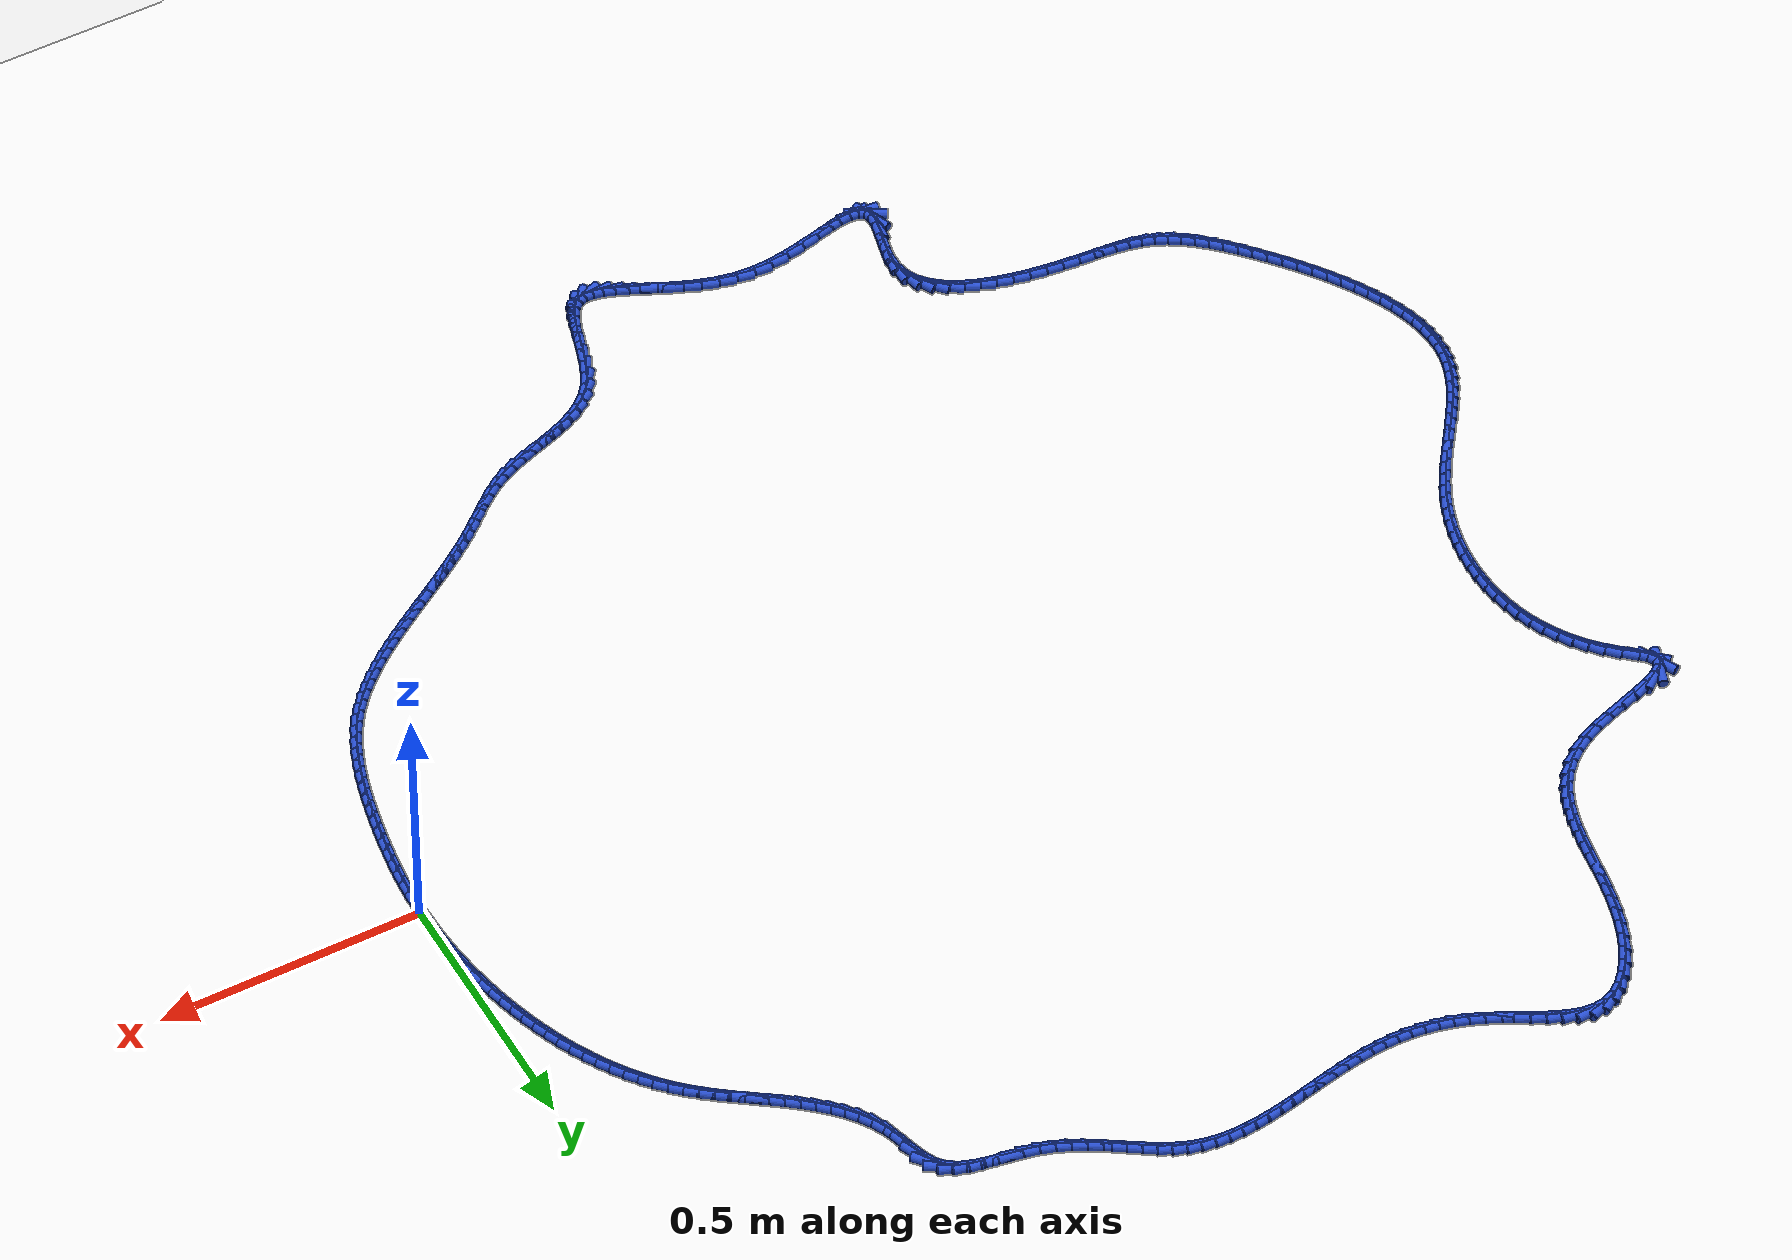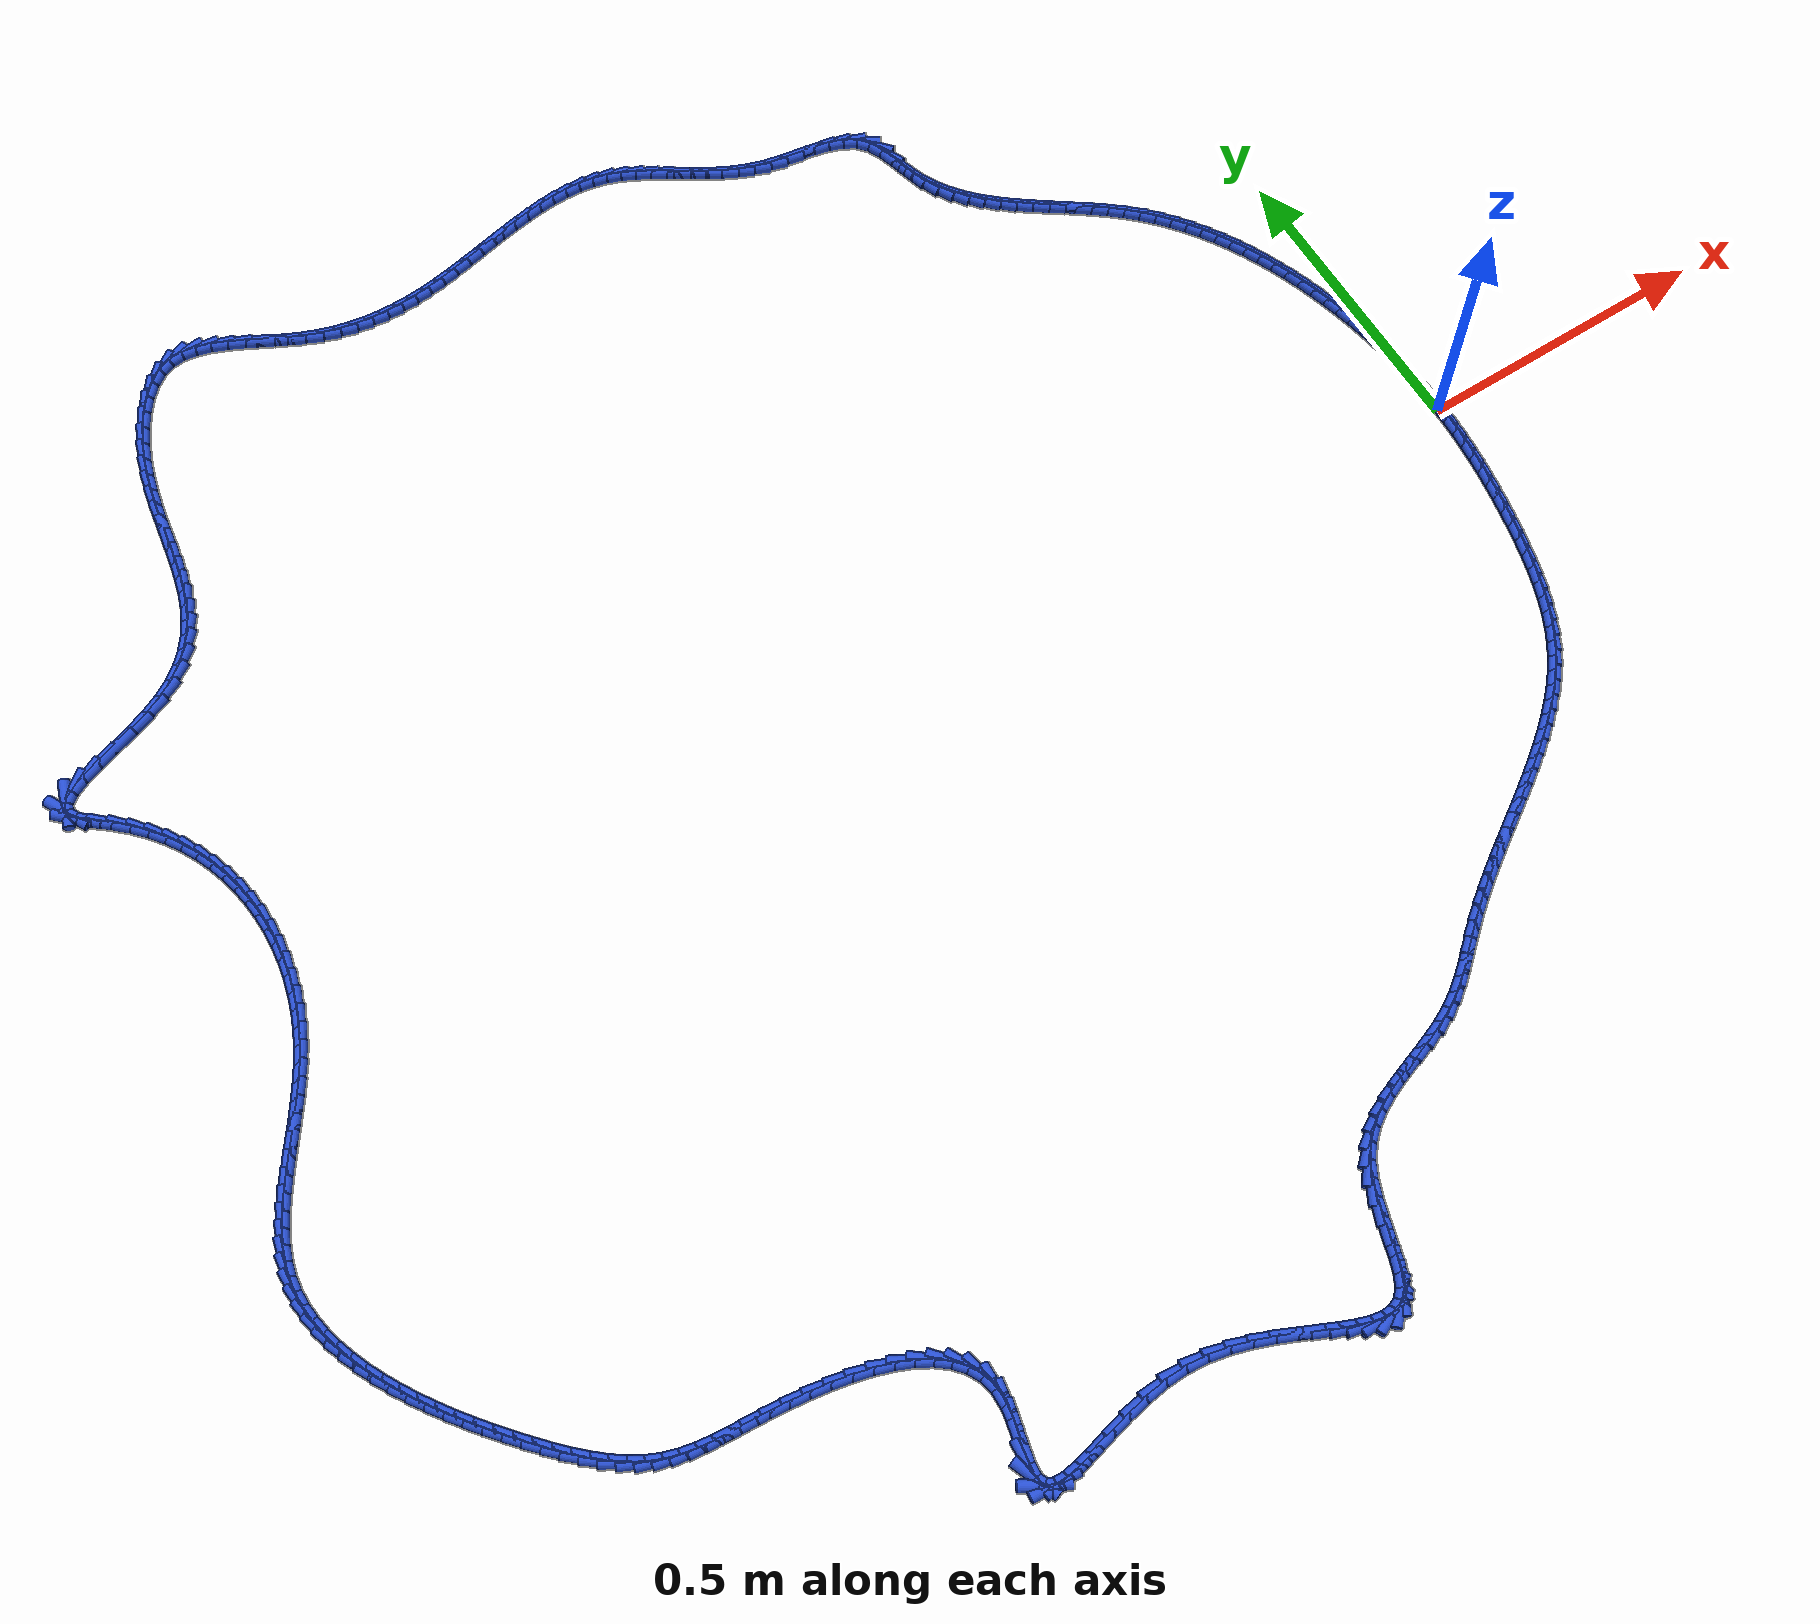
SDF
<sdf version="1.6">
 <world name="default">
  <light name="sun" type="directional">
   <pose>0 0 10 0 -0 0</pose>
   <diffuse>0.8 0.8 0.8 1</diffuse>
   <specular>0.2 0.2 0.2 1</specular>
   <attenuation>
    <range>1000</range>
    <constant>0.9</constant>
    <linear>0.01</linear>
    <quadratic>0.001</quadratic>
   </attenuation>
   <direction>-0.5 0.1 -0.9</direction>
  </light>
  <model name="ground_plane">
   <static>1</static>
   <link name="link">
    <collision name="collision">
     <geometry><plane><normal>0 0 1</normal><size>100 100</size></plane></geometry>
     <surface><friction><ode><mu>100</mu><mu2>50</mu2></ode></friction></surface>
    </collision>
    <visual name="visual">
     <cast_shadows>0</cast_shadows>
     <geometry><plane><normal>0 0 1</normal><size>100 100</size></plane></geometry>
     <material>
      <script><uri>file://media/materials/scripts/gazebo.material</uri><name>Gazebo/WhiteGlow</name></script>
     </material>
    </visual>
   </link>
  </model>
  <gravity>0 0 -9.8</gravity>
  <magnetic_field>6e-06 2.3e-05 -4.2e-05</magnetic_field>
  <atmosphere type="adiabatic"/>
  <physics name="default_physics" default="0" type="ode">
   <max_step_size>0.001</max_step_size>
   <real_time_factor>1</real_time_factor>
   <real_time_update_rate>1000</real_time_update_rate>
  </physics>
  <scene><ambient>0.4 0.4 0.4 1</ambient><background>0.7 0.7 0.7 1</background><shadows>1</shadows></scene>
  <spherical_coordinates>
   <surface_model>EARTH_WGS84</surface_model>
   <latitude_deg>0</latitude_deg>
   <longitude_deg>0</longitude_deg>
   <elevation>0</elevation>
   <heading_deg>0</heading_deg>
  </spherical_coordinates>
  <model name="line">
   <link name="link_0">
    <pose>-3.903127820947816e-18 6.938893903907228e-18 0.01 0 1.57 -1.5632918332255343</pose>
    <collision name="collision">
     <geometry><cylinder><radius>0.01</radius><length>0.08</length></cylinder></geometry>
    </collision>
    <visual name="visual">
     <material>
      <script><name>Gazebo/Blue</name><uri>file://media/materials/scripts/gazebo.material</uri></script>
     </material>
     <geometry><cylinder><radius>0.01</radius><length>0.08</length></cylinder></geometry>
    </visual>
   </link>
   <link name="link_1">
    <pose>-0.00019707740323714366 0.026260759872894952 0.01 0 1.57 -1.5348100912403275</pose>
    <collision name="collision">
     <geometry><cylinder><radius>0.01</radius><length>0.08</length></cylinder></geometry>
    </collision>
    <visual name="visual">
     <material>
      <script><name>Gazebo/Blue</name><uri>file://media/materials/scripts/gazebo.material</uri></script>
     </material>
     <geometry><cylinder><radius>0.01</radius><length>0.08</length></cylinder></geometry>
    </visual>
   </link>
   <link name="link_2">
    <pose>-0.0011432870485328023 0.052543063242601565 0.01 0 1.57 -1.5065970498066714</pose>
    <collision name="collision">
     <geometry><cylinder><radius>0.01</radius><length>0.08</length></cylinder></geometry>
    </collision>
    <visual name="visual">
     <material>
      <script><name>Gazebo/Blue</name><uri>file://media/materials/scripts/gazebo.material</uri></script>
     </material>
     <geometry><cylinder><radius>0.01</radius><length>0.08</length></cylinder></geometry>
    </visual>
   </link>
   <link name="link_3">
    <pose>-0.0028335343778641726 0.07883501893921417 0.01 0 1.57 -1.4786571732701919</pose>
    <collision name="collision">
     <geometry><cylinder><radius>0.01</radius><length>0.08</length></cylinder></geometry>
    </collision>
    <visual name="visual">
     <material>
      <script><name>Gazebo/Blue</name><uri>file://media/materials/scripts/gazebo.material</uri></script>
     </material>
     <geometry><cylinder><radius>0.01</radius><length>0.08</length></cylinder></geometry>
    </visual>
   </link>
   <link name="link_4">
    <pose>-0.005262724833208455 0.105124735792827 0.01 0 1.57 -1.4509934167091272</pose>
    <collision name="collision">
     <geometry><cylinder><radius>0.01</radius><length>0.08</length></cylinder></geometry>
    </collision>
    <visual name="visual">
     <material>
      <script><name>Gazebo/Blue</name><uri>file://media/materials/scripts/gazebo.material</uri></script>
     </material>
     <geometry><cylinder><radius>0.01</radius><length>0.08</length></cylinder></geometry>
    </visual>
   </link>
   <link name="link_5">
    <pose>-0.00842576385654285 0.13140032263353443 0.01 0 1.57 -1.423607314683148</pose>
    <collision name="collision">
     <geometry><cylinder><radius>0.01</radius><length>0.08</length></cylinder></geometry>
    </collision>
    <visual name="visual">
     <material>
      <script><name>Gazebo/Blue</name><uri>file://media/materials/scripts/gazebo.material</uri></script>
     </material>
     <geometry><cylinder><radius>0.01</radius><length>0.08</length></cylinder></geometry>
    </visual>
   </link>
   <link name="link_6">
    <pose>-0.012317556889844556 0.15764988829143067 0.01 0 1.57 -1.3964990755157327</pose>
    <collision name="collision">
     <geometry><cylinder><radius>0.01</radius><length>0.08</length></cylinder></geometry>
    </collision>
    <visual name="visual">
     <material>
      <script><name>Gazebo/Blue</name><uri>file://media/materials/scripts/gazebo.material</uri></script>
     </material>
     <geometry><cylinder><radius>0.01</radius><length>0.08</length></cylinder></geometry>
    </visual>
   </link>
   <link name="link_7">
    <pose>-0.016933009375090766 0.18386154159661003 0.01 0 1.57 -1.3696676792484899</pose>
    <collision name="collision">
     <geometry><cylinder><radius>0.01</radius><length>0.08</length></cylinder></geometry>
    </collision>
    <visual name="visual">
     <material>
      <script><name>Gazebo/Blue</name><uri>file://media/materials/scripts/gazebo.material</uri></script>
     </material>
     <geometry><cylinder><radius>0.01</radius><length>0.08</length></cylinder></geometry>
    </visual>
   </link>
   <link name="link_8">
    <pose>-0.022267026754258682 0.21002339137916679 0.01 0 1.57 -1.3430749311705588</pose>
    <collision name="collision">
     <geometry><cylinder><radius>0.01</radius><length>0.08</length></cylinder></geometry>
    </collision>
    <visual name="visual">
     <material>
      <script><name>Gazebo/Blue</name><uri>file://media/materials/scripts/gazebo.material</uri></script>
     </material>
     <geometry><cylinder><radius>0.01</radius><length>0.08</length></cylinder></geometry>
    </visual>
   </link>
   <link name="link_9">
    <pose>-0.028315247651225908 0.23612243249978096 0.01 0 1.57 -1.3159479446725486</pose>
    <collision name="collision">
     <geometry><cylinder><radius>0.01</radius><length>0.08</length></cylinder></geometry>
    </collision>
    <visual name="visual">
     <material>
      <script><name>Gazebo/Blue</name><uri>file://media/materials/scripts/gazebo.material</uri></script>
     </material>
     <geometry><cylinder><radius>0.01</radius><length>0.08</length></cylinder></geometry>
    </visual>
   </link>
   <link name="link_10">
    <pose>-0.03508858656389403 0.2621224502221293 0.01 0 1.57 -1.287490120131343</pose>
    <collision name="collision">
     <geometry><cylinder><radius>0.01</radius><length>0.08</length></cylinder></geometry>
    </collision>
    <visual name="visual">
     <material>
      <script><name>Gazebo/Blue</name><uri>file://media/materials/scripts/gazebo.material</uri></script>
     </material>
     <geometry><cylinder><radius>0.01</radius><length>0.08</length></cylinder></geometry>
    </visual>
   </link>
   <link name="link_11">
    <pose>-0.042612400836581264 0.287965285884167 0.01 0 1.57 -1.2575686136234239</pose>
    <collision name="collision">
     <geometry><cylinder><radius>0.01</radius><length>0.08</length></cylinder></geometry>
    </collision>
    <visual name="visual">
     <material>
      <script><name>Gazebo/Blue</name><uri>file://media/materials/scripts/gazebo.material</uri></script>
     </material>
     <geometry><cylinder><radius>0.01</radius><length>0.08</length></cylinder></geometry>
    </visual>
   </link>
   <link name="link_12">
    <pose>-0.05091261422573993 0.3135919202382389 0.01 0 1.57 -1.2260781231189402</pose>
    <collision name="collision">
     <geometry><cylinder><radius>0.01</radius><length>0.08</length></cylinder></geometry>
    </collision>
    <visual name="visual">
     <material>
      <script><name>Gazebo/Blue</name><uri>file://media/materials/scripts/gazebo.material</uri></script>
     </material>
     <geometry><cylinder><radius>0.01</radius><length>0.08</length></cylinder></geometry>
    </visual>
   </link>
   <link name="link_13">
    <pose>-0.06001515048782225 0.3389433340366903 0.01 0 1.57 -1.1929145746544014</pose>
    <collision name="collision">
     <geometry><cylinder><radius>0.01</radius><length>0.08</length></cylinder></geometry>
    </collision>
    <visual name="visual">
     <material>
      <script><name>Gazebo/Blue</name><uri>file://media/materials/scripts/gazebo.material</uri></script>
     </material>
     <geometry><cylinder><radius>0.01</radius><length>0.08</length></cylinder></geometry>
    </visual>
   </link>
   <link name="link_14">
    <pose>-0.06994593337928051 0.36396050803186597 0.01 0 1.57 -1.1579772439037401</pose>
    <collision name="collision">
     <geometry><cylinder><radius>0.01</radius><length>0.08</length></cylinder></geometry>
    </collision>
    <visual name="visual">
     <material>
      <script><name>Gazebo/Blue</name><uri>file://media/materials/scripts/gazebo.material</uri></script>
     </material>
     <geometry><cylinder><radius>0.01</radius><length>0.08</length></cylinder></geometry>
    </visual>
   </link>
   <link name="link_15">
    <pose>-0.08073088665656702 0.3885844229761109 0.01 0 1.57 -1.1211715505549253</pose>
    <collision name="collision">
     <geometry><cylinder><radius>0.01</radius><length>0.08</length></cylinder></geometry>
    </collision>
    <visual name="visual">
     <material>
      <script><name>Gazebo/Blue</name><uri>file://media/materials/scripts/gazebo.material</uri></script>
     </material>
     <geometry><cylinder><radius>0.01</radius><length>0.08</length></cylinder></geometry>
    </visual>
   </link>
   <link name="link_16">
    <pose>-0.09239593407613399 0.41275605962177025 0.01 0 1.57 -1.0824125986927136</pose>
    <collision name="collision">
     <geometry><cylinder><radius>0.01</radius><length>0.08</length></cylinder></geometry>
    </collision>
    <visual name="visual">
     <material>
      <script><name>Gazebo/Blue</name><uri>file://media/materials/scripts/gazebo.material</uri></script>
     </material>
     <geometry><cylinder><radius>0.01</radius><length>0.08</length></cylinder></geometry>
    </visual>
   </link>
   <link name="link_17">
    <pose>-0.10496699939443374 0.436416398721189 0.01 0 1.57 -1.041629505000383</pose>
    <collision name="collision">
     <geometry><cylinder><radius>0.01</radius><length>0.08</length></cylinder></geometry>
    </collision>
    <visual name="visual">
     <material>
      <script><name>Gazebo/Blue</name><uri>file://media/materials/scripts/gazebo.material</uri></script>
     </material>
     <geometry><cylinder><radius>0.01</radius><length>0.08</length></cylinder></geometry>
    </visual>
   </link>
   <link name="link_18">
    <pose>-0.11847000636791846 0.4595064210267119 0.01 0 1.57 -0.9987705007700904</pose>
    <collision name="collision">
     <geometry><cylinder><radius>0.01</radius><length>0.08</length></cylinder></geometry>
    </collision>
    <visual name="visual">
     <material>
      <script><name>Gazebo/Blue</name><uri>file://media/materials/scripts/gazebo.material</uri></script>
     </material>
     <geometry><cylinder><radius>0.01</radius><length>0.08</length></cylinder></geometry>
    </visual>
   </link>
   <link name="link_19">
    <pose>-0.13293087875304055 0.4819671072906843 0.01 0 1.57 -0.9538087080306736</pose>
    <collision name="collision">
     <geometry><cylinder><radius>0.01</radius><length>0.08</length></cylinder></geometry>
    </collision>
    <visual name="visual">
     <material>
      <script><name>Gazebo/Blue</name><uri>file://media/materials/scripts/gazebo.material</uri></script>
     </material>
     <geometry><cylinder><radius>0.01</radius><length>0.08</length></cylinder></geometry>
    </visual>
   </link>
   <link name="link_20">
    <pose>-0.14837554030625222 0.5037394382654511 0.01 0 1.57 -0.9067483722386667</pose>
    <collision name="collision">
     <geometry><cylinder><radius>0.01</radius><length>0.08</length></cylinder></geometry>
    </collision>
    <visual name="visual">
     <material>
      <script><name>Gazebo/Blue</name><uri>file://media/materials/scripts/gazebo.material</uri></script>
     </material>
     <geometry><cylinder><radius>0.01</radius><length>0.08</length></cylinder></geometry>
    </visual>
   </link>
   <link name="link_21">
    <pose>-0.16482991478400572 0.5247643947033572 0.01 0 1.57 -0.8576311879347525</pose>
    <collision name="collision">
     <geometry><cylinder><radius>0.01</radius><length>0.08</length></cylinder></geometry>
    </collision>
    <visual name="visual">
     <material>
      <script><name>Gazebo/Blue</name><uri>file://media/materials/scripts/gazebo.material</uri></script>
     </material>
     <geometry><cylinder><radius>0.01</radius><length>0.08</length></cylinder></geometry>
    </visual>
   </link>
   <link name="link_22">
    <pose>-0.1823199259427533 0.5449829573567477 0.01 0 1.57 -0.8065421935312231</pose>
    <collision name="collision">
     <geometry><cylinder><radius>0.01</radius><length>0.08</length></cylinder></geometry>
    </collision>
    <visual name="visual">
     <material>
      <script><name>Gazebo/Blue</name><uri>file://media/materials/scripts/gazebo.material</uri></script>
     </material>
     <geometry><cylinder><radius>0.01</radius><length>0.08</length></cylinder></geometry>
    </visual>
   </link>
   <link name="link_23">
    <pose>-0.20087149753894729 0.5643361069779674 0.01 0 1.57 -0.753617153168695</pose>
    <collision name="collision">
     <geometry><cylinder><radius>0.01</radius><length>0.08</length></cylinder></geometry>
    </collision>
    <visual name="visual">
     <material>
      <script><name>Gazebo/Blue</name><uri>file://media/materials/scripts/gazebo.material</uri></script>
     </material>
     <geometry><cylinder><radius>0.01</radius><length>0.08</length></cylinder></geometry>
    </visual>
   </link>
   <link name="link_24">
    <pose>-0.22051050218696697 0.5827648719619772 0.01 0 1.57 -0.702441004706767</pose>
    <collision name="collision">
     <geometry><cylinder><radius>0.01</radius><length>0.08</length></cylinder></geometry>
    </collision>
    <visual name="visual">
     <material>
      <script><name>Gazebo/Blue</name><uri>file://media/materials/scripts/gazebo.material</uri></script>
     </material>
     <geometry><cylinder><radius>0.01</radius><length>0.08</length></cylinder></geometry>
    </visual>
   </link>
   <link name="link_25">
    <pose>-0.24119487580690083 0.600273568748473 0.01 0 1.57 -0.6630655062927479</pose>
    <collision name="collision">
     <geometry><cylinder><radius>0.01</radius><length>0.08</length></cylinder></geometry>
    </collision>
    <visual name="visual">
     <material>
      <script><name>Gazebo/Blue</name><uri>file://media/materials/scripts/gazebo.material</uri></script>
     </material>
     <geometry><cylinder><radius>0.01</radius><length>0.08</length></cylinder></geometry>
    </visual>
   </link>
   <link name="link_26">
    <pose>-0.2626806670416635 0.6170545866759398 0.01 0 1.57 -0.6369563342111731</pose>
    <collision name="collision">
     <geometry><cylinder><radius>0.01</radius><length>0.08</length></cylinder></geometry>
    </collision>
    <visual name="visual">
     <material>
      <script><name>Gazebo/Blue</name><uri>file://media/materials/scripts/gazebo.material</uri></script>
     </material>
     <geometry><cylinder><radius>0.01</radius><length>0.08</length></cylinder></geometry>
    </visual>
   </link>
   <link name="link_27">
    <pose>-0.28468659432093846 0.6333350909316083 0.01 0 1.57 -0.6237539647634536</pose>
    <collision name="collision">
     <geometry><cylinder><radius>0.01</radius><length>0.08</length></cylinder></geometry>
    </collision>
    <visual name="visual">
     <material>
      <script><name>Gazebo/Blue</name><uri>file://media/materials/scripts/gazebo.material</uri></script>
     </material>
     <geometry><cylinder><radius>0.01</radius><length>0.08</length></cylinder></geometry>
    </visual>
   </link>
   <link name="link_28">
    <pose>-0.3069313760744094 0.6493422467027092 0.01 0 1.57 -0.623289311417262</pose>
    <collision name="collision">
     <geometry><cylinder><radius>0.01</radius><length>0.08</length></cylinder></geometry>
    </collision>
    <visual name="visual">
     <material>
      <script><name>Gazebo/Blue</name><uri>file://media/materials/scripts/gazebo.material</uri></script>
     </material>
     <geometry><cylinder><radius>0.01</radius><length>0.08</length></cylinder></geometry>
    </visual>
   </link>
   <link name="link_29">
    <pose>-0.32913373073175983 0.6653032191764736 0.01 0 1.57 -0.6356440025285129</pose>
    <collision name="collision">
     <geometry><cylinder><radius>0.01</radius><length>0.08</length></cylinder></geometry>
    </collision>
    <visual name="visual">
     <material>
      <script><name>Gazebo/Blue</name><uri>file://media/materials/scripts/gazebo.material</uri></script>
     </material>
     <geometry><cylinder><radius>0.01</radius><length>0.08</length></cylinder></geometry>
    </visual>
   </link>
   <link name="link_30">
    <pose>-0.3510123767226733 0.6814451735401323 0.01 0 1.57 -0.6611581090499187</pose>
    <collision name="collision">
     <geometry><cylinder><radius>0.01</radius><length>0.08</length></cylinder></geometry>
    </collision>
    <visual name="visual">
     <material>
      <script><name>Gazebo/Blue</name><uri>file://media/materials/scripts/gazebo.material</uri></script>
     </material>
     <geometry><cylinder><radius>0.01</radius><length>0.08</length></cylinder></geometry>
    </visual>
   </link>
   <link name="link_31">
    <pose>-0.37228603247683356 0.697995274980916 0.01 0 1.57 -0.7003831370044646</pose>
    <collision name="collision">
     <geometry><cylinder><radius>0.01</radius><length>0.08</length></cylinder></geometry>
    </collision>
    <visual name="visual">
     <material>
      <script><name>Gazebo/Blue</name><uri>file://media/materials/scripts/gazebo.material</uri></script>
     </material>
     <geometry><cylinder><radius>0.01</radius><length>0.08</length></cylinder></geometry>
    </visual>
   </link>
   <link name="link_32">
    <pose>-0.39267341642392384 0.7151806886860556 0.01 0 1.57 -0.7539620228355137</pose>
    <collision name="collision">
     <geometry><cylinder><radius>0.01</radius><length>0.08</length></cylinder></geometry>
    </collision>
    <visual name="visual">
     <material>
      <script><name>Gazebo/Blue</name><uri>file://media/materials/scripts/gazebo.material</uri></script>
     </material>
     <geometry><cylinder><radius>0.01</radius><length>0.08</length></cylinder></geometry>
    </visual>
   </link>
   <link name="link_33">
    <pose>-0.41189324699362784 0.7332285798427817 0.01 0 1.57 -0.8224062552509539</pose>
    <collision name="collision">
     <geometry><cylinder><radius>0.01</radius><length>0.08</length></cylinder></geometry>
    </collision>
    <visual name="visual">
     <material>
      <script><name>Gazebo/Blue</name><uri>file://media/materials/scripts/gazebo.material</uri></script>
     </material>
     <geometry><cylinder><radius>0.01</radius><length>0.08</length></cylinder></geometry>
    </visual>
   </link>
   <link name="link_34">
    <pose>-0.4296642426156293 0.7523661136383257 0.01 0 1.57 -0.9057463648109343</pose>
    <collision name="collision">
     <geometry><cylinder><radius>0.01</radius><length>0.08</length></cylinder></geometry>
    </collision>
    <visual name="visual">
     <material>
      <script><name>Gazebo/Blue</name><uri>file://media/materials/scripts/gazebo.material</uri></script>
     </material>
     <geometry><cylinder><radius>0.01</radius><length>0.08</length></cylinder></geometry>
    </visual>
   </link>
   <link name="link_35">
    <pose>-0.4457051217196115 0.7728204552599179 0.01 0 1.57 -1.0030791591129404</pose>
    <collision name="collision">
     <geometry><cylinder><radius>0.01</radius><length>0.08</length></cylinder></geometry>
    </collision>
    <visual name="visual">
     <material>
      <script><name>Gazebo/Blue</name><uri>file://media/materials/scripts/gazebo.material</uri></script>
     </material>
     <geometry><cylinder><radius>0.01</radius><length>0.08</length></cylinder></geometry>
    </visual>
   </link>
   <link name="link_36">
    <pose>-0.4597346027352581 0.7948187698947893 0.01 0 1.57 -1.1121397618428095</pose>
    <collision name="collision">
     <geometry><cylinder><radius>0.01</radius><length>0.08</length></cylinder></geometry>
    </collision>
    <visual name="visual">
     <material>
      <script><name>Gazebo/Blue</name><uri>file://media/materials/scripts/gazebo.material</uri></script>
     </material>
     <geometry><cylinder><radius>0.01</radius><length>0.08</length></cylinder></geometry>
    </visual>
   </link>
   <link name="link_37">
    <pose>-0.47147140409225285 0.8185882227301708 0.01 0 1.57 -1.2277286352811019</pose>
    <collision name="collision">
     <geometry><cylinder><radius>0.01</radius><length>0.08</length></cylinder></geometry>
    </collision>
    <visual name="visual">
     <material>
      <script><name>Gazebo/Blue</name><uri>file://media/materials/scripts/gazebo.material</uri></script>
     </material>
     <geometry><cylinder><radius>0.01</radius><length>0.08</length></cylinder></geometry>
    </visual>
   </link>
   <link name="link_38">
    <pose>-0.48066493686973966 0.8443265592550228 0.01 0 1.57 -1.2996597589890848</pose>
    <collision name="collision">
     <geometry><cylinder><radius>0.01</radius><length>0.08</length></cylinder></geometry>
    </collision>
    <visual name="visual">
     <material>
      <script><name>Gazebo/Blue</name><uri>file://media/materials/scripts/gazebo.material</uri></script>
     </material>
     <geometry><cylinder><radius>0.01</radius><length>0.08</length></cylinder></geometry>
    </visual>
   </link>
   <link name="link_39">
    <pose>-0.48813642993797896 0.8712041598865475 0.01 0 1.57 -1.27503638557698</pose>
    <collision name="collision">
     <geometry><cylinder><radius>0.01</radius><length>0.08</length></cylinder></geometry>
    </collision>
    <visual name="visual">
     <material>
      <script><name>Gazebo/Blue</name><uri>file://media/materials/scripts/gazebo.material</uri></script>
     </material>
     <geometry><cylinder><radius>0.01</radius><length>0.08</length></cylinder></geometry>
    </visual>
   </link>
   <link name="link_40">
    <pose>-0.49603303935109755 0.8971204695455494 0.01 0 1.57 -1.1369674884240284</pose>
    <collision name="collision">
     <geometry><cylinder><radius>0.01</radius><length>0.08</length></cylinder></geometry>
    </collision>
    <visual name="visual">
     <material>
      <script><name>Gazebo/Blue</name><uri>file://media/materials/scripts/gazebo.material</uri></script>
     </material>
     <geometry><cylinder><radius>0.01</radius><length>0.08</length></cylinder></geometry>
    </visual>
   </link>
   <link name="link_41">
    <pose>-0.5065841579201086 0.9198961070945805 0.01 0 1.57 -0.8568703562322579</pose>
    <collision name="collision">
     <geometry><cylinder><radius>0.01</radius><length>0.08</length></cylinder></geometry>
    </collision>
    <visual name="visual">
     <material>
      <script><name>Gazebo/Blue</name><uri>file://media/materials/scripts/gazebo.material</uri></script>
     </material>
     <geometry><cylinder><radius>0.01</radius><length>0.08</length></cylinder></geometry>
    </visual>
   </link>
   <link name="link_42">
    <pose>-0.521856120005676 0.937523467976326 0.01 0 1.57 -0.5541727263473782</pose>
    <collision name="collision">
     <geometry><cylinder><radius>0.01</radius><length>0.08</length></cylinder></geometry>
    </collision>
    <visual name="visual">
     <material>
      <script><name>Gazebo/Blue</name><uri>file://media/materials/scripts/gazebo.material</uri></script>
     </material>
     <geometry><cylinder><radius>0.01</radius><length>0.08</length></cylinder></geometry>
    </visual>
   </link>
   <link name="link_43">
    <pose>-0.5420136787500056 0.9499981993377099 0.01 0 1.57 -0.3448551654596596</pose>
    <collision name="collision">
     <geometry><cylinder><radius>0.01</radius><length>0.08</length></cylinder></geometry>
    </collision>
    <visual name="visual">
     <material>
      <script><name>Gazebo/Blue</name><uri>file://media/materials/scripts/gazebo.material</uri></script>
     </material>
     <geometry><cylinder><radius>0.01</radius><length>0.08</length></cylinder></geometry>
    </visual>
   </link>
   <link name="link_44">
    <pose>-0.5659918928999403 0.9586113899135802 0.01 0 1.57 -0.2232366668856001</pose>
    <collision name="collision">
     <geometry><cylinder><radius>0.01</radius><length>0.08</length></cylinder></geometry>
    </collision>
    <visual name="visual">
     <material>
      <script><name>Gazebo/Blue</name><uri>file://media/materials/scripts/gazebo.material</uri></script>
     </material>
     <geometry><cylinder><radius>0.01</radius><length>0.08</length></cylinder></geometry>
    </visual>
   </link>
   <link name="link_45">
    <pose>-0.5927051970663787 0.9646758552706846 0.01 0 1.57 -0.16862572748127758</pose>
    <collision name="collision">
     <geometry><cylinder><radius>0.01</radius><length>0.08</length></cylinder></geometry>
    </collision>
    <visual name="visual">
     <material>
      <script><name>Gazebo/Blue</name><uri>file://media/materials/scripts/gazebo.material</uri></script>
     </material>
     <geometry><cylinder><radius>0.01</radius><length>0.08</length></cylinder></geometry>
    </visual>
   </link>
   <link name="link_46">
    <pose>-0.6210680258602197 0.9695044109757711 0.01 0 1.57 -0.16798383813372617</pose>
    <collision name="collision">
     <geometry><cylinder><radius>0.01</radius><length>0.08</length></cylinder></geometry>
    </collision>
    <visual name="visual">
     <material>
      <script><name>Gazebo/Blue</name><uri>file://media/materials/scripts/gazebo.material</uri></script>
     </material>
     <geometry><cylinder><radius>0.01</radius><length>0.08</length></cylinder></geometry>
    </visual>
   </link>
   <link name="link_47">
    <pose>-0.649994813892362 0.9744098725955884 0.01 0 1.57 -0.21809588610812755</pose>
    <collision name="collision">
     <geometry><cylinder><radius>0.01</radius><length>0.08</length></cylinder></geometry>
    </collision>
    <visual name="visual">
     <material>
      <script><name>Gazebo/Blue</name><uri>file://media/materials/scripts/gazebo.material</uri></script>
     </material>
     <geometry><cylinder><radius>0.01</radius><length>0.08</length></cylinder></geometry>
    </visual>
   </link>
   <link name="link_48">
    <pose>-0.6783999957737047 0.9807050556968839 0.01 0 1.57 -0.31346826993457216</pose>
    <collision name="collision">
     <geometry><cylinder><radius>0.01</radius><length>0.08</length></cylinder></geometry>
    </collision>
    <visual name="visual">
     <material>
      <script><name>Gazebo/Blue</name><uri>file://media/materials/scripts/gazebo.material</uri></script>
     </material>
     <geometry><cylinder><radius>0.01</radius><length>0.08</length></cylinder></geometry>
    </visual>
   </link>
   <link name="link_49">
    <pose>-0.7053775544619353 0.9894499911024626 0.01 0 1.57 -0.4071397368359691</pose>
    <collision name="collision">
     <geometry><cylinder><radius>0.01</radius><length>0.08</length></cylinder></geometry>
    </collision>
    <visual name="visual">
     <material>
      <script><name>Gazebo/Blue</name><uri>file://media/materials/scripts/gazebo.material</uri></script>
     </material>
     <geometry><cylinder><radius>0.01</radius><length>0.08</length></cylinder></geometry>
    </visual>
   </link>
   <link name="link_50">
    <pose>-0.7309063504535626 1.0004588973173276 0.01 0 1.57 -0.4811946413412693</pose>
    <collision name="collision">
     <geometry><cylinder><radius>0.01</radius><length>0.08</length></cylinder></geometry>
    </collision>
    <visual name="visual">
     <material>
      <script><name>Gazebo/Blue</name><uri>file://media/materials/scripts/gazebo.material</uri></script>
     </material>
     <geometry><cylinder><radius>0.01</radius><length>0.08</length></cylinder></geometry>
    </visual>
   </link>
   <link name="link_51">
    <pose>-0.7552373757681212 1.0131628609569527 0.01 0 1.57 -0.5340883040986776</pose>
    <collision name="collision">
     <geometry><cylinder><radius>0.01</radius><length>0.08</length></cylinder></geometry>
    </collision>
    <visual name="visual">
     <material>
      <script><name>Gazebo/Blue</name><uri>file://media/materials/scripts/gazebo.material</uri></script>
     </material>
     <geometry><cylinder><radius>0.01</radius><length>0.08</length></cylinder></geometry>
    </visual>
   </link>
   <link name="link_52">
    <pose>-0.7786216968149536 1.0269928639039727 0.01 0 1.57 -0.5651204793994682</pose>
    <collision name="collision">
     <geometry><cylinder><radius>0.01</radius><length>0.08</length></cylinder></geometry>
    </collision>
    <visual name="visual">
     <material>
      <script><name>Gazebo/Blue</name><uri>file://media/materials/scripts/gazebo.material</uri></script>
     </material>
     <geometry><cylinder><radius>0.01</radius><length>0.08</length></cylinder></geometry>
    </visual>
   </link>
   <link name="link_53">
    <pose>-0.8013103800034015 1.041379888041021 0.01 0 1.57 -0.5737272041077568</pose>
    <collision name="collision">
     <geometry><cylinder><radius>0.01</radius><length>0.08</length></cylinder></geometry>
    </collision>
    <visual name="visual">
     <material>
      <script><name>Gazebo/Blue</name><uri>file://media/materials/scripts/gazebo.material</uri></script>
     </material>
     <geometry><cylinder><radius>0.01</radius><length>0.08</length></cylinder></geometry>
    </visual>
   </link>
   <link name="link_54">
    <pose>-0.8235544917428067 1.0557549152507315 0.01 0 1.57 -0.5590030396459621</pose>
    <collision name="collision">
     <geometry><cylinder><radius>0.01</radius><length>0.08</length></cylinder></geometry>
    </collision>
    <visual name="visual">
     <material>
      <script><name>Gazebo/Blue</name><uri>file://media/materials/scripts/gazebo.material</uri></script>
     </material>
     <geometry><cylinder><radius>0.01</radius><length>0.08</length></cylinder></geometry>
    </visual>
   </link>
   <link name="link_55">
    <pose>-0.845605098442512 1.069548927415739 0.01 0 1.57 -0.5195122546426327</pose>
    <collision name="collision">
     <geometry><cylinder><radius>0.01</radius><length>0.08</length></cylinder></geometry>
    </collision>
    <visual name="visual">
     <material>
      <script><name>Gazebo/Blue</name><uri>file://media/materials/scripts/gazebo.material</uri></script>
     </material>
     <geometry><cylinder><radius>0.01</radius><length>0.08</length></cylinder></geometry>
    </visual>
   </link>
   <link name="link_56">
    <pose>-0.8677132665118586 1.0821929064186773 0.01 0 1.57 -0.4534801786071243</pose>
    <collision name="collision">
     <geometry><cylinder><radius>0.01</radius><length>0.08</length></cylinder></geometry>
    </collision>
    <visual name="visual">
     <material>
      <script><name>Gazebo/Blue</name><uri>file://media/materials/scripts/gazebo.material</uri></script>
     </material>
     <geometry><cylinder><radius>0.01</radius><length>0.08</length></cylinder></geometry>
    </visual>
   </link>
   <link name="link_57">
    <pose>-0.8901300623601892 1.09311783414218 0.01 0 1.57 -0.35956090834249355</pose>
    <collision name="collision">
     <geometry><cylinder><radius>0.01</radius><length>0.08</length></cylinder></geometry>
    </collision>
    <visual name="visual">
     <material>
      <script><name>Gazebo/Blue</name><uri>file://media/materials/scripts/gazebo.material</uri></script>
     </material>
     <geometry><cylinder><radius>0.01</radius><length>0.08</length></cylinder></geometry>
    </visual>
   </link>
   <link name="link_58">
    <pose>-0.9131065385099231 1.1017547290400438 0.01 0 1.57 -0.24590019628507445</pose>
    <collision name="collision">
     <geometry><cylinder><radius>0.01</radius><length>0.08</length></cylinder></geometry>
    </collision>
    <visual name="visual">
     <material>
      <script><name>Gazebo/Blue</name><uri>file://media/materials/scripts/gazebo.material</uri></script>
     </material>
     <geometry><cylinder><radius>0.01</radius><length>0.08</length></cylinder></geometry>
    </visual>
   </link>
   <link name="link_59">
    <pose>-0.9368278021111154 1.107708276475724 0.01 0 1.57 -0.14027447071063578</pose>
    <collision name="collision">
     <geometry><cylinder><radius>0.01</radius><length>0.08</length></cylinder></geometry>
    </collision>
    <visual name="visual">
     <material>
      <script><name>Gazebo/Blue</name><uri>file://media/materials/scripts/gazebo.material</uri></script>
     </material>
     <geometry><cylinder><radius>0.01</radius><length>0.08</length></cylinder></geometry>
    </visual>
   </link>
   <link name="link_60">
    <pose>-0.9612605930659535 1.1111582312034196 0.01 0 1.57 -0.04962777685539173</pose>
    <collision name="collision">
     <geometry><cylinder><radius>0.01</radius><length>0.08</length></cylinder></geometry>
    </collision>
    <visual name="visual">
     <material>
      <script><name>Gazebo/Blue</name><uri>file://media/materials/scripts/gazebo.material</uri></script>
     </material>
     <geometry><cylinder><radius>0.01</radius><length>0.08</length></cylinder></geometry>
    </visual>
   </link>
   <link name="link_61">
    <pose>-0.9863265130445336 1.112403219355165 0.01 0 1.57 0.025807520179779886</pose>
    <collision name="collision">
     <geometry><cylinder><radius>0.01</radius><length>0.08</length></cylinder></geometry>
    </collision>
    <visual name="visual">
     <material>
      <script><name>Gazebo/Blue</name><uri>file://media/materials/scripts/gazebo.material</uri></script>
     </material>
     <geometry><cylinder><radius>0.01</radius><length>0.08</length></cylinder></geometry>
    </visual>
   </link>
   <link name="link_62">
    <pose>-1.0119471637169515 1.1117418670629946 0.01 0 1.57 0.08672935312643844</pose>
    <collision name="collision">
     <geometry><cylinder><radius>0.01</radius><length>0.08</length></cylinder></geometry>
    </collision>
    <visual name="visual">
     <material>
      <script><name>Gazebo/Blue</name><uri>file://media/materials/scripts/gazebo.material</uri></script>
     </material>
     <geometry><cylinder><radius>0.01</radius><length>0.08</length></cylinder></geometry>
    </visual>
   </link>
   <link name="link_63">
    <pose>-1.0380441467533035 1.1094728004589425 0.01 0 1.57 0.13423843441653208</pose>
    <collision name="collision">
     <geometry><cylinder><radius>0.01</radius><length>0.08</length></cylinder></geometry>
    </collision>
    <visual name="visual">
     <material>
      <script><name>Gazebo/Blue</name><uri>file://media/materials/scripts/gazebo.material</uri></script>
     </material>
     <geometry><cylinder><radius>0.01</radius><length>0.08</length></cylinder></geometry>
    </visual>
   </link>
   <link name="link_64">
    <pose>-1.064539063823685 1.1058946456750434 0.01 0 1.57 0.16948312236743976</pose>
    <collision name="collision">
     <geometry><cylinder><radius>0.01</radius><length>0.08</length></cylinder></geometry>
    </collision>
    <visual name="visual">
     <material>
      <script><name>Gazebo/Blue</name><uri>file://media/materials/scripts/gazebo.material</uri></script>
     </material>
     <geometry><cylinder><radius>0.01</radius><length>0.08</length></cylinder></geometry>
    </visual>
   </link>
   <link name="link_65">
    <pose>-1.0913535165981916 1.1013060288433316 0.01 0 1.57 0.19345951035670922</pose>
    <collision name="collision">
     <geometry><cylinder><radius>0.01</radius><length>0.08</length></cylinder></geometry>
    </collision>
    <visual name="visual">
     <material>
      <script><name>Gazebo/Blue</name><uri>file://media/materials/scripts/gazebo.material</uri></script>
     </material>
     <geometry><cylinder><radius>0.01</radius><length>0.08</length></cylinder></geometry>
    </visual>
   </link>
   <link name="link_66">
    <pose>-1.1184091067469206 1.0960055760958423 0.01 0 1.57 0.20691525059108806</pose>
    <collision name="collision">
     <geometry><cylinder><radius>0.01</radius><length>0.08</length></cylinder></geometry>
    </collision>
    <visual name="visual">
     <material>
      <script><name>Gazebo/Blue</name><uri>file://media/materials/scripts/gazebo.material</uri></script>
     </material>
     <geometry><cylinder><radius>0.01</radius><length>0.08</length></cylinder></geometry>
    </visual>
   </link>
   <link name="link_67">
    <pose>-1.1456274359399665 1.090291913564608 0.01 0 1.57 0.21031138225236334</pose>
    <collision name="collision">
     <geometry><cylinder><radius>0.01</radius><length>0.08</length></cylinder></geometry>
    </collision>
    <visual name="visual">
     <material>
      <script><name>Gazebo/Blue</name><uri>file://media/materials/scripts/gazebo.material</uri></script>
     </material>
     <geometry><cylinder><radius>0.01</radius><length>0.08</length></cylinder></geometry>
    </visual>
   </link>
   <link name="link_68">
    <pose>-1.172930105847426 1.084463667381665 0.01 0 1.57 0.20381240524735147</pose>
    <collision name="collision">
     <geometry><cylinder><radius>0.01</radius><length>0.08</length></cylinder></geometry>
    </collision>
    <visual name="visual">
     <material>
      <script><name>Gazebo/Blue</name><uri>file://media/materials/scripts/gazebo.material</uri></script>
     </material>
     <geometry><cylinder><radius>0.01</radius><length>0.08</length></cylinder></geometry>
    </visual>
   </link>
   <link name="link_69">
    <pose>-1.2002387181393948 1.078819463679047 0.01 0 1.57 0.1872893701793756</pose>
    <collision name="collision">
     <geometry><cylinder><radius>0.01</radius><length>0.08</length></cylinder></geometry>
    </collision>
    <visual name="visual">
     <material>
      <script><name>Gazebo/Blue</name><uri>file://media/materials/scripts/gazebo.material</uri></script>
     </material>
     <geometry><cylinder><radius>0.01</radius><length>0.08</length></cylinder></geometry>
    </visual>
   </link>
   <link name="link_70">
    <pose>-1.2274748744859691 1.073657928588788 0.01 0 1.57 0.16033206831747765</pose>
    <collision name="collision">
     <geometry><cylinder><radius>0.01</radius><length>0.08</length></cylinder></geometry>
    </collision>
    <visual name="visual">
     <material>
      <script><name>Gazebo/Blue</name><uri>file://media/materials/scripts/gazebo.material</uri></script>
     </material>
     <geometry><cylinder><radius>0.01</radius><length>0.08</length></cylinder></geometry>
    </visual>
   </link>
   <link name="link_71">
    <pose>-1.2545601765572443 1.0692776882429227 0.01 0 1.57 0.12227672520900765</pose>
    <collision name="collision">
     <geometry><cylinder><radius>0.01</radius><length>0.08</length></cylinder></geometry>
    </collision>
    <visual name="visual">
     <material>
      <script><name>Gazebo/Blue</name><uri>file://media/materials/scripts/gazebo.material</uri></script>
     </material>
     <geometry><cylinder><radius>0.01</radius><length>0.08</length></cylinder></geometry>
    </visual>
   </link>
   <link name="link_72">
    <pose>-1.2814162379447962 1.0659773521533977 0.01 0 1.57 0.07366379797271562</pose>
    <collision name="collision">
     <geometry><cylinder><radius>0.01</radius><length>0.08</length></cylinder></geometry>
    </collision>
    <visual name="visual">
     <material>
      <script><name>Gazebo/Blue</name><uri>file://media/materials/scripts/gazebo.material</uri></script>
     </material>
     <geometry><cylinder><radius>0.01</radius><length>0.08</length></cylinder></geometry>
    </visual>
   </link>
   <link name="link_73">
    <pose>-1.3079929842341942 1.0640160592426624 0.01 0 1.57 0.01849449668090897</pose>
    <collision name="collision">
     <geometry><cylinder><radius>0.01</radius><length>0.08</length></cylinder></geometry>
    </collision>
    <visual name="visual">
     <material>
      <script><name>Gazebo/Blue</name><uri>file://media/materials/scripts/gazebo.material</uri></script>
     </material>
     <geometry><cylinder><radius>0.01</radius><length>0.08</length></cylinder></geometry>
    </visual>
   </link>
   <link name="link_74">
    <pose>-1.3343293009269745 1.0635289267790975 0.01 0 1.57 -0.04195459647967384</pose>
    <collision name="collision">
     <geometry><cylinder><radius>0.01</radius><length>0.08</length></cylinder></geometry>
    </collision>
    <visual name="visual">
     <material>
      <script><name>Gazebo/Blue</name><uri>file://media/materials/scripts/gazebo.material</uri></script>
     </material>
     <geometry><cylinder><radius>0.01</radius><length>0.08</length></cylinder></geometry>
    </visual>
   </link>
   <link name="link_75">
    <pose>-1.360481500913151 1.064626775992571 0.01 0 1.57 -0.10693792218226808</pose>
    <collision name="collision">
     <geometry><cylinder><radius>0.01</radius><length>0.08</length></cylinder></geometry>
    </collision>
    <visual name="visual">
     <material>
      <script><name>Gazebo/Blue</name><uri>file://media/materials/scripts/gazebo.material</uri></script>
     </material>
     <geometry><cylinder><radius>0.01</radius><length>0.08</length></cylinder></geometry>
    </visual>
   </link>
   <link name="link_76">
    <pose>-1.3865058970827357 1.0674204281129498 0.01 0 1.57 -0.17543259551412074</pose>
    <collision name="collision">
     <geometry><cylinder><radius>0.01</radius><length>0.08</length></cylinder></geometry>
    </collision>
    <visual name="visual">
     <material>
      <script><name>Gazebo/Blue</name><uri>file://media/materials/scripts/gazebo.material</uri></script>
     </material>
     <geometry><cylinder><radius>0.01</radius><length>0.08</length></cylinder></geometry>
    </visual>
   </link>
   <link name="link_77">
    <pose>-1.4124588023257405 1.0720207043701007 0.01 0 1.57 -0.24618625247893214</pose>
    <collision name="collision">
     <geometry><cylinder><radius>0.01</radius><length>0.08</length></cylinder></geometry>
    </collision>
    <visual name="visual">
     <material>
      <script><name>Gazebo/Blue</name><uri>file://media/materials/scripts/gazebo.material</uri></script>
     </material>
     <geometry><cylinder><radius>0.01</radius><length>0.08</length></cylinder></geometry>
    </visual>
   </link>
   <link name="link_78">
    <pose>-1.4383965295321783 1.0785384259938915 0.01 0 1.57 -0.3178087703347083</pose>
    <collision name="collision">
     <geometry><cylinder><radius>0.01</radius><length>0.08</length></cylinder></geometry>
    </collision>
    <visual name="visual">
     <material>
      <script><name>Gazebo/Blue</name><uri>file://media/materials/scripts/gazebo.material</uri></script>
     </material>
     <geometry><cylinder><radius>0.01</radius><length>0.08</length></cylinder></geometry>
    </visual>
   </link>
   <link name="link_79">
    <pose>-1.4643753915920605 1.087084414214189 0.01 0 1.57 -0.38888700737513526</pose>
    <collision name="collision">
     <geometry><cylinder><radius>0.01</radius><length>0.08</length></cylinder></geometry>
    </collision>
    <visual name="visual">
     <material>
      <script><name>Gazebo/Blue</name><uri>file://media/materials/scripts/gazebo.material</uri></script>
     </material>
     <geometry><cylinder><radius>0.01</radius><length>0.08</length></cylinder></geometry>
    </visual>
   </link>
   <link name="link_80">
    <pose>-1.490451662887468 1.0977692826484264 0.01 0 1.57 -0.45076342057396274</pose>
    <collision name="collision">
     <geometry><cylinder><radius>0.01</radius><length>0.08</length></cylinder></geometry>
    </collision>
    <visual name="visual">
     <material>
      <script><name>Gazebo/Blue</name><uri>file://media/materials/scripts/gazebo.material</uri></script>
     </material>
     <geometry><cylinder><radius>0.01</radius><length>0.08</length></cylinder></geometry>
    </visual>
   </link>
   <link name="link_81">
    <pose>-1.5166328868240058 1.1104409157558592 0.01 0 1.57 -0.4834780568722597</pose>
    <collision name="collision">
     <geometry><cylinder><radius>0.01</radius><length>0.08</length></cylinder></geometry>
    </collision>
    <visual name="visual">
     <material>
      <script><name>Gazebo/Blue</name><uri>file://media/materials/scripts/gazebo.material</uri></script>
     </material>
     <geometry><cylinder><radius>0.01</radius><length>0.08</length></cylinder></geometry>
    </visual>
   </link>
   <link name="link_82">
    <pose>-1.5427825495077094 1.1241705245985811 0.01 0 1.57 -0.48614760413924757</pose>
    <collision name="collision">
     <geometry><cylinder><radius>0.01</radius><length>0.08</length></cylinder></geometry>
    </collision>
    <visual name="visual">
     <material>
      <script><name>Gazebo/Blue</name><uri>file://media/materials/scripts/gazebo.material</uri></script>
     </material>
     <geometry><cylinder><radius>0.01</radius><length>0.08</length></cylinder></geometry>
    </visual>
   </link>
   <link name="link_83">
    <pose>-1.5687376451167458 1.137886491130577 0.01 0 1.57 -0.45838159572695697</pose>
    <collision name="collision">
     <geometry><cylinder><radius>0.01</radius><length>0.08</length></cylinder></geometry>
    </collision>
    <visual name="visual">
     <material>
      <script><name>Gazebo/Blue</name><uri>file://media/materials/scripts/gazebo.material</uri></script>
     </material>
     <geometry><cylinder><radius>0.01</radius><length>0.08</length></cylinder></geometry>
    </visual>
   </link>
   <link name="link_84">
    <pose>-1.5943351678292839 1.1505171973058326 0.01 0 1.57 -0.39564370857243153</pose>
    <collision name="collision">
     <geometry><cylinder><radius>0.01</radius><length>0.08</length></cylinder></geometry>
    </collision>
    <visual name="visual">
     <material>
      <script><name>Gazebo/Blue</name><uri>file://media/materials/scripts/gazebo.material</uri></script>
     </material>
     <geometry><cylinder><radius>0.01</radius><length>0.08</length></cylinder></geometry>
    </visual>
   </link>
   <link name="link_85">
    <pose>-1.6194121118234899 1.1609910250783326 0.01 0 1.57 -0.2887212035658918</pose>
    <collision name="collision">
     <geometry><cylinder><radius>0.01</radius><length>0.08</length></cylinder></geometry>
    </collision>
    <visual name="visual">
     <material>
      <script><name>Gazebo/Blue</name><uri>file://media/materials/scripts/gazebo.material</uri></script>
     </material>
     <geometry><cylinder><radius>0.01</radius><length>0.08</length></cylinder></geometry>
    </visual>
   </link>
   <link name="link_86">
    <pose>-1.6438054712775327 1.1682363564020628 0.01 0 1.57 -0.12443321736092114</pose>
    <collision name="collision">
     <geometry><cylinder><radius>0.01</radius><length>0.08</length></cylinder></geometry>
    </collision>
    <visual name="visual">
     <material>
      <script><name>Gazebo/Blue</name><uri>file://media/materials/scripts/gazebo.material</uri></script>
     </material>
     <geometry><cylinder><radius>0.01</radius><length>0.08</length></cylinder></geometry>
    </visual>
   </link>
   <link name="link_87">
    <pose>-1.6673522403695804 1.171181573231009 0.01 0 1.57 0.1072540975397198</pose>
    <collision name="collision">
     <geometry><cylinder><radius>0.01</radius><length>0.08</length></cylinder></geometry>
    </collision>
    <visual name="visual">
     <material>
      <script><name>Gazebo/Blue</name><uri>file://media/materials/scripts/gazebo.material</uri></script>
     </material>
     <geometry><cylinder><radius>0.01</radius><length>0.08</length></cylinder></geometry>
    </visual>
   </link>
   <link name="link_88">
    <pose>-1.6898894132777995 1.1687550575191552 0.01 0 1.57 0.3829025991499241</pose>
    <collision name="collision">
     <geometry><cylinder><radius>0.01</radius><length>0.08</length></cylinder></geometry>
    </collision>
    <visual name="visual">
     <material>
      <script><name>Gazebo/Blue</name><uri>file://media/materials/scripts/gazebo.material</uri></script>
     </material>
     <geometry><cylinder><radius>0.01</radius><length>0.08</length></cylinder></geometry>
    </visual>
   </link>
   <link name="link_89">
    <pose>-1.7112537111671742 1.160149896697818 0.01 0 1.57 0.6180912399512815</pose>
    <collision name="collision">
     <geometry><cylinder><radius>0.01</radius><length>0.08</length></cylinder></geometry>
    </collision>
    <visual name="visual">
     <material>
      <script><name>Gazebo/Blue</name><uri>file://media/materials/scripts/gazebo.material</uri></script>
     </material>
     <geometry><cylinder><radius>0.01</radius><length>0.08</length></cylinder></geometry>
    </visual>
   </link>
   <link name="link_90">
    <pose>-1.731280461728366 1.145910249525942 0.01 0 1.57 0.7954433825808381</pose>
    <collision name="collision">
     <geometry><cylinder><radius>0.01</radius><length>0.08</length></cylinder></geometry>
    </collision>
    <visual name="visual">
     <material>
      <script><name>Gazebo/Blue</name><uri>file://media/materials/scripts/gazebo.material</uri></script>
     </material>
     <geometry><cylinder><radius>0.01</radius><length>0.08</length></cylinder></geometry>
    </visual>
   </link>
   <link name="link_91">
    <pose>-1.7498045492173258 1.1270102158923476 0.01 0 1.57 0.9296596730885333</pose>
    <collision name="collision">
     <geometry><cylinder><radius>0.01</radius><length>0.08</length></cylinder></geometry>
    </collision>
    <visual name="visual">
     <material>
      <script><name>Gazebo/Blue</name><uri>file://media/materials/scripts/gazebo.material</uri></script>
     </material>
     <geometry><cylinder><radius>0.01</radius><length>0.08</length></cylinder></geometry>
    </visual>
   </link>
   <link name="link_92">
    <pose>-1.7666608577035119 1.1044240765032207 0.01 0 1.57 1.0349048048263865</pose>
    <collision name="collision">
     <geometry><cylinder><radius>0.01</radius><length>0.08</length></cylinder></geometry>
    </collision>
    <visual name="visual">
     <material>
      <script><name>Gazebo/Blue</name><uri>file://media/materials/scripts/gazebo.material</uri></script>
     </material>
     <geometry><cylinder><radius>0.01</radius><length>0.08</length></cylinder></geometry>
    </visual>
   </link>
   <link name="link_93">
    <pose>-1.7816842712563823 1.0791261120647444 0.01 0 1.57 1.1218236097301866</pose>
    <collision name="collision">
     <geometry><cylinder><radius>0.01</radius><length>0.08</length></cylinder></geometry>
    </collision>
    <visual name="visual">
     <material>
      <script><name>Gazebo/Blue</name><uri>file://media/materials/scripts/gazebo.material</uri></script>
     </material>
     <geometry><cylinder><radius>0.01</radius><length>0.08</length></cylinder></geometry>
    </visual>
   </link>
   <link name="link_94">
    <pose>-1.794709673945396 1.0520906032831028 0.01 0 1.57 1.198138277703248</pose>
    <collision name="collision">
     <geometry><cylinder><radius>0.01</radius><length>0.08</length></cylinder></geometry>
    </collision>
    <visual name="visual">
     <material>
      <script><name>Gazebo/Blue</name><uri>file://media/materials/scripts/gazebo.material</uri></script>
     </material>
     <geometry><cylinder><radius>0.01</radius><length>0.08</length></cylinder></geometry>
    </visual>
   </link>
   <link name="link_95">
    <pose>-1.805583946855302 1.0242737741907078 0.01 0 1.57 1.2654658841827975</pose>
    <collision name="collision">
     <geometry><cylinder><radius>0.01</radius><length>0.08</length></cylinder></geometry>
    </collision>
    <visual name="visual">
     <material>
      <script><name>Gazebo/Blue</name><uri>file://media/materials/scripts/gazebo.material</uri></script>
     </material>
     <geometry><cylinder><radius>0.01</radius><length>0.08</length></cylinder></geometry>
    </visual>
   </link>
   <link name="link_96">
    <pose>-1.814424771334167 0.9962242681098383 0.01 0 1.57 1.3205122938195741</pose>
    <collision name="collision">
     <geometry><cylinder><radius>0.01</radius><length>0.08</length></cylinder></geometry>
    </collision>
    <visual name="visual">
     <material>
      <script><name>Gazebo/Blue</name><uri>file://media/materials/scripts/gazebo.material</uri></script>
     </material>
     <geometry><cylinder><radius>0.01</radius><length>0.08</length></cylinder></geometry>
    </visual>
   </link>
   <link name="link_97">
    <pose>-1.821617808695458 0.9680873924750515 0.01 0 1.57 1.362367591236169</pose>
    <collision name="collision">
     <geometry><cylinder><radius>0.01</radius><length>0.08</length></cylinder></geometry>
    </collision>
    <visual name="visual">
     <material>
      <script><name>Gazebo/Blue</name><uri>file://media/materials/scripts/gazebo.material</uri></script>
     </material>
     <geometry><cylinder><radius>0.01</radius><length>0.08</length></cylinder></geometry>
    </visual>
   </link>
   <link name="link_98">
    <pose>-1.827560153188969 0.9399912470407871 0.01 0 1.57 1.3905597705814599</pose>
    <collision name="collision">
     <geometry><cylinder><radius>0.01</radius><length>0.08</length></cylinder></geometry>
    </collision>
    <visual name="visual">
     <material>
      <script><name>Gazebo/Blue</name><uri>file://media/materials/scripts/gazebo.material</uri></script>
     </material>
     <geometry><cylinder><radius>0.01</radius><length>0.08</length></cylinder></geometry>
    </visual>
   </link>
   <link name="link_99">
    <pose>-1.8326488990644938 0.9120639315614852 0.01 0 1.57 1.4046907873138161</pose>
    <collision name="collision">
     <geometry><cylinder><radius>0.01</radius><length>0.08</length></cylinder></geometry>
    </collision>
    <visual name="visual">
     <material>
      <script><name>Gazebo/Blue</name><uri>file://media/materials/scripts/gazebo.material</uri></script>
     </material>
     <geometry><cylinder><radius>0.01</radius><length>0.08</length></cylinder></geometry>
    </visual>
   </link>
   <link name="link_100">
    <pose>-1.8372811405718263 0.8844335457915853 0.01 0 1.57 1.4042672857266112</pose>
    <collision name="collision">
     <geometry><cylinder><radius>0.01</radius><length>0.08</length></cylinder></geometry>
    </collision>
    <visual name="visual">
     <material>
      <script><name>Gazebo/Blue</name><uri>file://media/materials/scripts/gazebo.material</uri></script>
     </material>
     <geometry><cylinder><radius>0.01</radius><length>0.08</length></cylinder></geometry>
    </visual>
   </link>
   <link name="link_101">
    <pose>-1.8418539719607592 0.8572281894855277 0.01 0 1.57 1.3885955473438962</pose>
    <collision name="collision">
     <geometry><cylinder><radius>0.01</radius><length>0.08</length></cylinder></geometry>
    </collision>
    <visual name="visual">
     <material>
      <script><name>Gazebo/Blue</name><uri>file://media/materials/scripts/gazebo.material</uri></script>
     </material>
     <geometry><cylinder><radius>0.01</radius><length>0.08</length></cylinder></geometry>
    </visual>
   </link>
   <link name="link_102">
    <pose>-1.8467644874810876 0.8305759623977523 0.01 0 1.57 1.356756793644323</pose>
    <collision name="collision">
     <geometry><cylinder><radius>0.01</radius><length>0.08</length></cylinder></geometry>
    </collision>
    <visual name="visual">
     <material>
      <script><name>Gazebo/Blue</name><uri>file://media/materials/scripts/gazebo.material</uri></script>
     </material>
     <geometry><cylinder><radius>0.01</radius><length>0.08</length></cylinder></geometry>
    </visual>
   </link>
   <link name="link_103">
    <pose>-1.8524097813826046 0.8046049642826988 0.01 0 1.57 1.307695210429977</pose>
    <collision name="collision">
     <geometry><cylinder><radius>0.01</radius><length>0.08</length></cylinder></geometry>
    </collision>
    <visual name="visual">
     <material>
      <script><name>Gazebo/Blue</name><uri>file://media/materials/scripts/gazebo.material</uri></script>
     </material>
     <geometry><cylinder><radius>0.01</radius><length>0.08</length></cylinder></geometry>
    </visual>
   </link>
   <link name="link_104">
    <pose>-1.859186947915104 0.7794432948948063 0.01 0 1.57 1.2404738764128573</pose>
    <collision name="collision">
     <geometry><cylinder><radius>0.01</radius><length>0.08</length></cylinder></geometry>
    </collision>
    <visual name="visual">
     <material>
      <script><name>Gazebo/Blue</name><uri>file://media/materials/scripts/gazebo.material</uri></script>
     </material>
     <geometry><cylinder><radius>0.01</radius><length>0.08</length></cylinder></geometry>
    </visual>
   </link>
   <link name="link_105">
    <pose>-1.8674930813283803 0.7552190539885163 0.01 0 1.57 1.154758013641637</pose>
    <collision name="collision">
     <geometry><cylinder><radius>0.01</radius><length>0.08</length></cylinder></geometry>
    </collision>
    <visual name="visual">
     <material>
      <script><name>Gazebo/Blue</name><uri>file://media/materials/scripts/gazebo.material</uri></script>
     </material>
     <geometry><cylinder><radius>0.01</radius><length>0.08</length></cylinder></geometry>
    </visual>
   </link>
   <link name="link_106">
    <pose>-1.877725275872226 0.7320603413182676 0.01 0 1.57 1.051517301723917</pose>
    <collision name="collision">
     <geometry><cylinder><radius>0.01</radius><length>0.08</length></cylinder></geometry>
    </collision>
    <visual name="visual">
     <material>
      <script><name>Gazebo/Blue</name><uri>file://media/materials/scripts/gazebo.material</uri></script>
     </material>
     <geometry><cylinder><radius>0.01</radius><length>0.08</length></cylinder></geometry>
    </visual>
   </link>
   <link name="link_107">
    <pose>-1.8902806257964355 0.7100952566385003 0.01 0 1.57 0.933741165543122</pose>
    <collision name="collision">
     <geometry><cylinder><radius>0.01</radius><length>0.08</length></cylinder></geometry>
    </collision>
    <visual name="visual">
     <material>
      <script><name>Gazebo/Blue</name><uri>file://media/materials/scripts/gazebo.material</uri></script>
     </material>
     <geometry><cylinder><radius>0.01</radius><length>0.08</length></cylinder></geometry>
    </visual>
   </link>
   <link name="link_108">
    <pose>-1.9055562253508023 0.6894518997036541 0.01 0 1.57 0.8066947869471024</pose>
    <collision name="collision">
     <geometry><cylinder><radius>0.01</radius><length>0.08</length></cylinder></geometry>
    </collision>
    <visual name="visual">
     <material>
      <script><name>Gazebo/Blue</name><uri>file://media/materials/scripts/gazebo.material</uri></script>
     </material>
     <geometry><cylinder><radius>0.01</radius><length>0.08</length></cylinder></geometry>
    </visual>
   </link>
   <link name="link_109">
    <pose>-1.923949168785121 0.6702583702681687 0.01 0 1.57 0.6772325279290158</pose>
    <collision name="collision">
     <geometry><cylinder><radius>0.01</radius><length>0.08</length></cylinder></geometry>
    </collision>
    <visual name="visual">
     <material>
      <script><name>Gazebo/Blue</name><uri>file://media/materials/scripts/gazebo.material</uri></script>
     </material>
     <geometry><cylinder><radius>0.01</radius><length>0.08</length></cylinder></geometry>
    </visual>
   </link>
   <link name="link_110">
    <pose>-1.9458565503491845 0.6526427680864846 0.01 0 1.57 0.5522450719808226</pose>
    <collision name="collision">
     <geometry><cylinder><radius>0.01</radius><length>0.08</length></cylinder></geometry>
    </collision>
    <visual name="visual">
     <material>
      <script><name>Gazebo/Blue</name><uri>file://media/materials/scripts/gazebo.material</uri></script>
     </material>
     <geometry><cylinder><radius>0.01</radius><length>0.08</length></cylinder></geometry>
    </visual>
   </link>
   <link name="link_111">
    <pose>-1.9716754642927867 0.6367331929130415 0.01 0 1.57 0.4380729368176899</pose>
    <collision name="collision">
     <geometry><cylinder><radius>0.01</radius><length>0.08</length></cylinder></geometry>
    </collision>
    <visual name="visual">
     <material>
      <script><name>Gazebo/Blue</name><uri>file://media/materials/scripts/gazebo.material</uri></script>
     </material>
     <geometry><cylinder><radius>0.01</radius><length>0.08</length></cylinder></geometry>
    </visual>
   </link>
   <link name="link_112">
    <pose>-2.001750527602216 0.622645176369293 0.01 0 1.57 0.35708903357712235</pose>
    <collision name="collision">
     <geometry><cylinder><radius>0.01</radius><length>0.08</length></cylinder></geometry>
    </collision>
    <visual name="visual">
     <material>
      <script><name>Gazebo/Blue</name><uri>file://media/materials/scripts/gazebo.material</uri></script>
     </material>
     <geometry><cylinder><radius>0.01</radius><length>0.08</length></cylinder></geometry>
    </visual>
   </link>
   <link name="link_113">
    <pose>-2.0351431948637075 0.6101869368783803 0.01 0 1.57 0.3179954676663819</pose>
    <collision name="collision">
     <geometry><cylinder><radius>0.01</radius><length>0.08</length></cylinder></geometry>
    </collision>
    <visual name="visual">
     <material>
      <script><name>Gazebo/Blue</name><uri>file://media/materials/scripts/gazebo.material</uri></script>
     </material>
     <geometry><cylinder><radius>0.01</radius><length>0.08</length></cylinder></geometry>
    </visual>
   </link>
   <link name="link_114">
    <pose>-2.069587949310113 0.5988488875640862 0.01 0 1.57 0.31319092149880345</pose>
    <collision name="collision">
     <geometry><cylinder><radius>0.01</radius><length>0.08</length></cylinder></geometry>
    </collision>
    <visual name="visual">
     <material>
      <script><name>Gazebo/Blue</name><uri>file://media/materials/scripts/gazebo.material</uri></script>
     </material>
     <geometry><cylinder><radius>0.01</radius><length>0.08</length></cylinder></geometry>
    </visual>
   </link>
   <link name="link_115">
    <pose>-2.102758032024388 0.5881067742555798 0.01 0 1.57 0.34632531178015946</pose>
    <collision name="collision">
     <geometry><cylinder><radius>0.01</radius><length>0.08</length></cylinder></geometry>
    </collision>
    <visual name="visual">
     <material>
      <script><name>Gazebo/Blue</name><uri>file://media/materials/scripts/gazebo.material</uri></script>
     </material>
     <geometry><cylinder><radius>0.01</radius><length>0.08</length></cylinder></geometry>
    </visual>
   </link>
   <link name="link_116">
    <pose>-2.13232668408949 0.5774363427820315 0.01 0 1.57 0.4397760986040028</pose>
    <collision name="collision">
     <geometry><cylinder><radius>0.01</radius><length>0.08</length></cylinder></geometry>
    </collision>
    <visual name="visual">
     <material>
      <script><name>Gazebo/Blue</name><uri>file://media/materials/scripts/gazebo.material</uri></script>
     </material>
     <geometry><cylinder><radius>0.01</radius><length>0.08</length></cylinder></geometry>
    </visual>
   </link>
   <link name="link_117">
    <pose>-2.155967146588373 0.5663133389726108 0.01 0 1.57 0.6664196601822986</pose>
    <collision name="collision">
     <geometry><cylinder><radius>0.01</radius><length>0.08</length></cylinder></geometry>
    </collision>
    <visual name="visual">
     <material>
      <script><name>Gazebo/Blue</name><uri>file://media/materials/scripts/gazebo.material</uri></script>
     </material>
     <geometry><cylinder><radius>0.01</radius><length>0.08</length></cylinder></geometry>
    </visual>
   </link>
   <link name="link_118">
    <pose>-2.1713526606039917 0.5542135086564879 0.01 0 1.57 1.2312758747828436</pose>
    <collision name="collision">
     <geometry><cylinder><radius>0.01</radius><length>0.08</length></cylinder></geometry>
    </collision>
    <visual name="visual">
     <material>
      <script><name>Gazebo/Blue</name><uri>file://media/materials/scripts/gazebo.material</uri></script>
     </material>
     <geometry><cylinder><radius>0.01</radius><length>0.08</length></cylinder></geometry>
    </visual>
   </link>
   <link name="link_119">
    <pose>-2.176156467219302 0.5406125976628321 0.01 0 1.57 -1.1016620722139232</pose>
    <collision name="collision">
     <geometry><cylinder><radius>0.01</radius><length>0.08</length></cylinder></geometry>
    </collision>
    <visual name="visual">
     <material>
      <script><name>Gazebo/Blue</name><uri>file://media/materials/scripts/gazebo.material</uri></script>
     </material>
     <geometry><cylinder><radius>0.01</radius><length>0.08</length></cylinder></geometry>
    </visual>
   </link>
   <link name="link_120">
    <pose>-2.1682459001231122 0.5250061224983977 0.01 0 1.57 -0.7605866039556429</pose>
    <collision name="collision">
     <geometry><cylinder><radius>0.01</radius><length>0.08</length></cylinder></geometry>
    </collision>
    <visual name="visual">
     <material>
      <script><name>Gazebo/Blue</name><uri>file://media/materials/scripts/gazebo.material</uri></script>
     </material>
     <geometry><cylinder><radius>0.01</radius><length>0.08</length></cylinder></geometry>
    </visual>
   </link>
   <link name="link_121">
    <pose>-2.1496531446004505 0.5073138401387255 0.01 0 1.57 -0.696909069863282</pose>
    <collision name="collision">
     <geometry><cylinder><radius>0.01</radius><length>0.08</length></cylinder></geometry>
    </collision>
    <visual name="visual">
     <material>
      <script><name>Gazebo/Blue</name><uri>file://media/materials/scripts/gazebo.material</uri></script>
     </material>
     <geometry><cylinder><radius>0.01</radius><length>0.08</length></cylinder></geometry>
    </visual>
   </link>
   <link name="link_122">
    <pose>-2.1264154596576854 0.48786347272061226 0.01 0 1.57 -0.7516819592958682</pose>
    <collision name="collision">
     <geometry><cylinder><radius>0.01</radius><length>0.08</length></cylinder></geometry>
    </collision>
    <visual name="visual">
     <material>
      <script><name>Gazebo/Blue</name><uri>file://media/materials/scripts/gazebo.material</uri></script>
     </material>
     <geometry><cylinder><radius>0.01</radius><length>0.08</length></cylinder></geometry>
    </visual>
   </link>
   <link name="link_123">
    <pose>-2.104069609490934 0.46697584395557784 0.01 0 1.57 -0.8371136397900096</pose>
    <collision name="collision">
     <geometry><cylinder><radius>0.01</radius><length>0.08</length></cylinder></geometry>
    </collision>
    <visual name="visual">
     <material>
      <script><name>Gazebo/Blue</name><uri>file://media/materials/scripts/gazebo.material</uri></script>
     </material>
     <geometry><cylinder><radius>0.01</radius><length>0.08</length></cylinder></geometry>
    </visual>
   </link>
   <link name="link_124">
    <pose>-2.0841023538976318 0.44482867721796104 0.01 0 1.57 -0.9226563671314962</pose>
    <collision name="collision">
     <geometry><cylinder><radius>0.01</radius><length>0.08</length></cylinder></geometry>
    </collision>
    <visual name="visual">
     <material>
      <script><name>Gazebo/Blue</name><uri>file://media/materials/scripts/gazebo.material</uri></script>
     </material>
     <geometry><cylinder><radius>0.01</radius><length>0.08</length></cylinder></geometry>
    </visual>
   </link>
   <link name="link_125">
    <pose>-2.0664707295997213 0.4215456455981145 0.01 0 1.57 -1.007557089426084</pose>
    <collision name="collision">
     <geometry><cylinder><radius>0.01</radius><length>0.08</length></cylinder></geometry>
    </collision>
    <visual name="visual">
     <material>
      <script><name>Gazebo/Blue</name><uri>file://media/materials/scripts/gazebo.material</uri></script>
     </material>
     <geometry><cylinder><radius>0.01</radius><length>0.08</length></cylinder></geometry>
    </visual>
   </link>
   <link name="link_126">
    <pose>-2.051128932225527 0.39725032180095526 0.01 0 1.57 -1.0912122643896338</pose>
    <collision name="collision">
     <geometry><cylinder><radius>0.01</radius><length>0.08</length></cylinder></geometry>
    </collision>
    <visual name="visual">
     <material>
      <script><name>Gazebo/Blue</name><uri>file://media/materials/scripts/gazebo.material</uri></script>
     </material>
     <geometry><cylinder><radius>0.01</radius><length>0.08</length></cylinder></geometry>
    </visual>
   </link>
   <link name="link_127">
    <pose>-2.038031157403375 0.37206627853140123 0.01 0 1.57 -1.173138957144604</pose>
    <collision name="collision">
     <geometry><cylinder><radius>0.01</radius><length>0.08</length></cylinder></geometry>
    </collision>
    <visual name="visual">
     <material>
      <script><name>Gazebo/Blue</name><uri>file://media/materials/scripts/gazebo.material</uri></script>
     </material>
     <geometry><cylinder><radius>0.01</radius><length>0.08</length></cylinder></geometry>
    </visual>
   </link>
   <link name="link_128">
    <pose>-2.0271316007615905 0.3461170884943695 0.01 0 1.57 -1.2529921801703066</pose>
    <collision name="collision">
     <geometry><cylinder><radius>0.01</radius><length>0.08</length></cylinder></geometry>
    </collision>
    <visual name="visual">
     <material>
      <script><name>Gazebo/Blue</name><uri>file://media/materials/scripts/gazebo.material</uri></script>
     </material>
     <geometry><cylinder><radius>0.01</radius><length>0.08</length></cylinder></geometry>
    </visual>
   </link>
   <link name="link_129">
    <pose>-2.018384457928499 0.31952632439477746 0.01 0 1.57 -1.330567826032644</pose>
    <collision name="collision">
     <geometry><cylinder><radius>0.01</radius><length>0.08</length></cylinder></geometry>
    </collision>
    <visual name="visual">
     <material>
      <script><name>Gazebo/Blue</name><uri>file://media/materials/scripts/gazebo.material</uri></script>
     </material>
     <geometry><cylinder><radius>0.01</radius><length>0.08</length></cylinder></geometry>
    </visual>
   </link>
   <link name="link_130">
    <pose>-2.0117439245324245 0.2924175589375423 0.01 0 1.57 -1.4057940189995712</pose>
    <collision name="collision">
     <geometry><cylinder><radius>0.01</radius><length>0.08</length></cylinder></geometry>
    </collision>
    <visual name="visual">
     <material>
      <script><name>Gazebo/Blue</name><uri>file://media/materials/scripts/gazebo.material</uri></script>
     </material>
     <geometry><cylinder><radius>0.01</radius><length>0.08</length></cylinder></geometry>
    </visual>
   </link>
   <link name="link_131">
    <pose>-2.007164196201694 0.264914364827581 0.01 0 1.57 -1.4787148780488113</pose>
    <collision name="collision">
     <geometry><cylinder><radius>0.01</radius><length>0.08</length></cylinder></geometry>
    </collision>
    <visual name="visual">
     <material>
      <script><name>Gazebo/Blue</name><uri>file://media/materials/scripts/gazebo.material</uri></script>
     </material>
     <geometry><cylinder><radius>0.01</radius><length>0.08</length></cylinder></geometry>
    </visual>
   </link>
   <link name="link_132">
    <pose>-2.0045994685646313 0.2371403147698119 0.01 0 1.57 -1.5494706606262796</pose>
    <collision name="collision">
     <geometry><cylinder><radius>0.01</radius><length>0.08</length></cylinder></geometry>
    </collision>
    <visual name="visual">
     <material>
      <script><name>Gazebo/Blue</name><uri>file://media/materials/scripts/gazebo.material</uri></script>
     </material>
     <geometry><cylinder><radius>0.01</radius><length>0.08</length></cylinder></geometry>
    </visual>
   </link>
   <link name="link_133">
    <pose>-2.004003937249563 0.20921898146915174 0.01 0 1.57 1.5233151840269976</pose>
    <collision name="collision">
     <geometry><cylinder><radius>0.01</radius><length>0.08</length></cylinder></geometry>
    </collision>
    <visual name="visual">
     <material>
      <script><name>Gazebo/Blue</name><uri>file://media/materials/scripts/gazebo.material</uri></script>
     </material>
     <geometry><cylinder><radius>0.01</radius><length>0.08</length></cylinder></geometry>
    </visual>
   </link>
   <link name="link_134">
    <pose>-2.0053317978848133 0.18127393763051786 0.01 0 1.57 1.4561840259172845</pose>
    <collision name="collision">
     <geometry><cylinder><radius>0.01</radius><length>0.08</length></cylinder></geometry>
    </collision>
    <visual name="visual">
     <material>
      <script><name>Gazebo/Blue</name><uri>file://media/materials/scripts/gazebo.material</uri></script>
     </material>
     <geometry><cylinder><radius>0.01</radius><length>0.08</length></cylinder></geometry>
    </visual>
   </link>
   <link name="link_135">
    <pose>-2.0085372460987085 0.15342875595882727 0.01 0 1.57 1.3904138535100525</pose>
    <collision name="collision">
     <geometry><cylinder><radius>0.01</radius><length>0.08</length></cylinder></geometry>
    </collision>
    <visual name="visual">
     <material>
      <script><name>Gazebo/Blue</name><uri>file://media/materials/scripts/gazebo.material</uri></script>
     </material>
     <geometry><cylinder><radius>0.01</radius><length>0.08</length></cylinder></geometry>
    </visual>
   </link>
   <link name="link_136">
    <pose>-2.013574477519573 0.1258070091589981 0.01 0 1.57 1.3256615088799972</pose>
    <collision name="collision">
     <geometry><cylinder><radius>0.01</radius><length>0.08</length></cylinder></geometry>
    </collision>
    <visual name="visual">
     <material>
      <script><name>Gazebo/Blue</name><uri>file://media/materials/scripts/gazebo.material</uri></script>
     </material>
     <geometry><cylinder><radius>0.01</radius><length>0.08</length></cylinder></geometry>
    </visual>
   </link>
   <link name="link_137">
    <pose>-2.0203976877757324 0.09853226993594727 0.01 0 1.57 1.2615654216429195</pose>
    <collision name="collision">
     <geometry><cylinder><radius>0.01</radius><length>0.08</length></cylinder></geometry>
    </collision>
    <visual name="visual">
     <material>
      <script><name>Gazebo/Blue</name><uri>file://media/materials/scripts/gazebo.material</uri></script>
     </material>
     <geometry><cylinder><radius>0.01</radius><length>0.08</length></cylinder></geometry>
    </visual>
   </link>
   <link name="link_138">
    <pose>-2.028961072495512 0.07172811099459214 0.01 0 1.57 1.197753498786396</pose>
    <collision name="collision">
     <geometry><cylinder><radius>0.01</radius><length>0.08</length></cylinder></geometry>
    </collision>
    <visual name="visual">
     <material>
      <script><name>Gazebo/Blue</name><uri>file://media/materials/scripts/gazebo.material</uri></script>
     </material>
     <geometry><cylinder><radius>0.01</radius><length>0.08</length></cylinder></geometry>
    </visual>
   </link>
   <link name="link_139">
    <pose>-2.039218827307237 0.045518105039850015 0.01 0 1.57 1.1339288257949294</pose>
    <collision name="collision">
     <geometry><cylinder><radius>0.01</radius><length>0.08</length></cylinder></geometry>
    </collision>
    <visual name="visual">
     <material>
      <script><name>Gazebo/Blue</name><uri>file://media/materials/scripts/gazebo.material</uri></script>
     </material>
     <geometry><cylinder><radius>0.01</radius><length>0.08</length></cylinder></geometry>
    </visual>
   </link>
   <link name="link_140">
    <pose>-2.051123338736102 0.020024428509412974 0.01 0 1.57 1.0744316281054078</pose>
    <collision name="collision">
     <geometry><cylinder><radius>0.01</radius><length>0.08</length></cylinder></geometry>
    </collision>
    <visual name="visual">
     <material>
      <script><name>Gazebo/Blue</name><uri>file://media/materials/scripts/gazebo.material</uri></script>
     </material>
     <geometry><cylinder><radius>0.01</radius><length>0.08</length></cylinder></geometry>
    </visual>
   </link>
   <link name="link_141">
    <pose>-2.0645207721327044 -0.004712723745425298 0.01 0 1.57 1.0263137775389735</pose>
    <collision name="collision">
     <geometry><cylinder><radius>0.01</radius><length>0.08</length></cylinder></geometry>
    </collision>
    <visual name="visual">
     <material>
      <script><name>Gazebo/Blue</name><uri>file://media/materials/scripts/gazebo.material</uri></script>
     </material>
     <geometry><cylinder><radius>0.01</radius><length>0.08</length></cylinder></geometry>
    </visual>
   </link>
   <link name="link_142">
    <pose>-2.0790939731737152 -0.028779207126630856 0.01 0 1.57 0.9900091788965728</pose>
    <collision name="collision">
     <geometry><cylinder><radius>0.01</radius><length>0.08</length></cylinder></geometry>
    </collision>
    <visual name="visual">
     <material>
      <script><name>Gazebo/Blue</name><uri>file://media/materials/scripts/gazebo.material</uri></script>
     </material>
     <geometry><cylinder><radius>0.01</radius><length>0.08</length></cylinder></geometry>
    </visual>
   </link>
   <link name="link_143">
    <pose>-2.09451189204711 -0.05227160158531137 0.01 0 1.57 0.9653043991538459</pose>
    <collision name="collision">
     <geometry><cylinder><radius>0.01</radius><length>0.08</length></cylinder></geometry>
    </collision>
    <visual name="visual">
     <material>
      <script><name>Gazebo/Blue</name><uri>file://media/materials/scripts/gazebo.material</uri></script>
     </material>
     <geometry><cylinder><radius>0.01</radius><length>0.08</length></cylinder></geometry>
    </visual>
   </link>
   <link name="link_144">
    <pose>-2.1104434789408644 -0.0752864870725746 0.01 0 1.57 0.9520963504807047</pose>
    <collision name="collision">
     <geometry><cylinder><radius>0.01</radius><length>0.08</length></cylinder></geometry>
    </collision>
    <visual name="visual">
     <material>
      <script><name>Gazebo/Blue</name><uri>file://media/materials/scripts/gazebo.material</uri></script>
     </material>
     <geometry><cylinder><radius>0.01</radius><length>0.08</length></cylinder></geometry>
    </visual>
   </link>
   <link name="link_145">
    <pose>-2.126557684042955 -0.09792044353952824 0.01 0 1.57 0.9504944550691583</pose>
    <collision name="collision">
     <geometry><cylinder><radius>0.01</radius><length>0.08</length></cylinder></geometry>
    </collision>
    <visual name="visual">
     <material>
      <script><name>Gazebo/Blue</name><uri>file://media/materials/scripts/gazebo.material</uri></script>
     </material>
     <geometry><cylinder><radius>0.01</radius><length>0.08</length></cylinder></geometry>
    </visual>
   </link>
   <link name="link_146">
    <pose>-2.1425234575413574 -0.12027005093728073 0.01 0 1.57 0.9608883282410815</pose>
    <collision name="collision">
     <geometry><cylinder><radius>0.01</radius><length>0.08</length></cylinder></geometry>
    </collision>
    <visual name="visual">
     <material>
      <script><name>Gazebo/Blue</name><uri>file://media/materials/scripts/gazebo.material</uri></script>
     </material>
     <geometry><cylinder><radius>0.01</radius><length>0.08</length></cylinder></geometry>
    </visual>
   </link>
   <link name="link_147">
    <pose>-2.1580097496240467 -0.1424318892169384 0.01 0 1.57 0.9839868110194508</pose>
    <collision name="collision">
     <geometry><cylinder><radius>0.01</radius><length>0.08</length></cylinder></geometry>
    </collision>
    <visual name="visual">
     <material>
      <script><name>Gazebo/Blue</name><uri>file://media/materials/scripts/gazebo.material</uri></script>
     </material>
     <geometry><cylinder><radius>0.01</radius><length>0.08</length></cylinder></geometry>
    </visual>
   </link>
   <link name="link_148">
    <pose>-2.1726855104790004 -0.16450253832960968 0.01 0 1.57 1.0208211946546906</pose>
    <collision name="collision">
     <geometry><cylinder><radius>0.01</radius><length>0.08</length></cylinder></geometry>
    </collision>
    <visual name="visual">
     <material>
      <script><name>Gazebo/Blue</name><uri>file://media/materials/scripts/gazebo.material</uri></script>
     </material>
     <geometry><cylinder><radius>0.01</radius><length>0.08</length></cylinder></geometry>
    </visual>
   </link>
   <link name="link_149">
    <pose>-2.1862196902941937 -0.1865785782264023 0.01 0 1.57 1.0726857452094924</pose>
    <collision name="collision">
     <geometry><cylinder><radius>0.01</radius><length>0.08</length></cylinder></geometry>
    </collision>
    <visual name="visual">
     <material>
      <script><name>Gazebo/Blue</name><uri>file://media/materials/scripts/gazebo.material</uri></script>
     </material>
     <geometry><cylinder><radius>0.01</radius><length>0.08</length></cylinder></geometry>
    </visual>
   </link>
   <link name="link_150">
    <pose>-2.1982812392576023 -0.20875658885842396 0.01 0 1.57 1.140962241953203</pose>
    <collision name="collision">
     <geometry><cylinder><radius>0.01</radius><length>0.08</length></cylinder></geometry>
    </collision>
    <visual name="visual">
     <material>
      <script><name>Gazebo/Blue</name><uri>file://media/materials/scripts/gazebo.material</uri></script>
     </material>
     <geometry><cylinder><radius>0.01</radius><length>0.08</length></cylinder></geometry>
    </visual>
   </link>
   <link name="link_151">
    <pose>-2.2085391075572023 -0.23113315017678238 0.01 0 1.57 1.2267515767455033</pose>
    <collision name="collision">
     <geometry><cylinder><radius>0.01</radius><length>0.08</length></cylinder></geometry>
    </collision>
    <visual name="visual">
     <material>
      <script><name>Gazebo/Blue</name><uri>file://media/materials/scripts/gazebo.material</uri></script>
     </material>
     <geometry><cylinder><radius>0.01</radius><length>0.08</length></cylinder></geometry>
    </visual>
   </link>
   <link name="link_152">
    <pose>-2.21666224538097 -0.2538048421325853 0.01 0 1.57 1.3302499300452797</pose>
    <collision name="collision">
     <geometry><cylinder><radius>0.01</radius><length>0.08</length></cylinder></geometry>
    </collision>
    <visual name="visual">
     <material>
      <script><name>Gazebo/Blue</name><uri>file://media/materials/scripts/gazebo.material</uri></script>
     </material>
     <geometry><cylinder><radius>0.01</radius><length>0.08</length></cylinder></geometry>
    </visual>
   </link>
   <link name="link_153">
    <pose>-2.222319603393628 -0.276868244514392 0.01 0 1.57 1.4461213831450492</pose>
    <collision name="collision">
     <geometry><cylinder><radius>0.01</radius><length>0.08</length></cylinder></geometry>
    </collision>
    <visual name="visual">
     <material>
      <script><name>Gazebo/Blue</name><uri>file://media/materials/scripts/gazebo.material</uri></script>
     </material>
     <geometry><cylinder><radius>0.01</radius><length>0.08</length></cylinder></geometry>
    </visual>
   </link>
   <link name="link_154">
    <pose>-2.2252674857395762 -0.30039015359786475 0.01 0 1.57 1.5571831872065396</pose>
    <collision name="collision">
     <geometry><cylinder><radius>0.01</radius><length>0.08</length></cylinder></geometry>
    </collision>
    <visual name="visual">
     <material>
      <script><name>Gazebo/Blue</name><uri>file://media/materials/scripts/gazebo.material</uri></script>
     </material>
     <geometry><cylinder><radius>0.01</radius><length>0.08</length></cylinder></geometry>
    </visual>
   </link>
   <link name="link_155">
    <pose>-2.2255933269958335 -0.32432446543366455 0.01 0 1.57 -1.4832588583455786</pose>
    <collision name="collision">
     <geometry><cylinder><radius>0.01</radius><length>0.08</length></cylinder></geometry>
    </collision>
    <visual name="visual">
     <material>
      <script><name>Gazebo/Blue</name><uri>file://media/materials/scripts/gazebo.material</uri></script>
     </material>
     <geometry><cylinder><radius>0.01</radius><length>0.08</length></cylinder></geometry>
    </visual>
   </link>
   <link name="link_156">
    <pose>-2.2234630102679604 -0.34859832873771074 0.01 0 1.57 -1.3925735281482696</pose>
    <collision name="collision">
     <geometry><cylinder><radius>0.01</radius><length>0.08</length></cylinder></geometry>
    </collision>
    <visual name="visual">
     <material>
      <script><name>Gazebo/Blue</name><uri>file://media/materials/scripts/gazebo.material</uri></script>
     </material>
     <geometry><cylinder><radius>0.01</radius><length>0.08</length></cylinder></geometry>
    </visual>
   </link>
   <link name="link_157">
    <pose>-2.2190424186615187 -0.3731388922259247 0.01 0 1.57 -1.312114643448786</pose>
    <collision name="collision">
     <geometry><cylinder><radius>0.01</radius><length>0.08</length></cylinder></geometry>
    </collision>
    <visual name="visual">
     <material>
      <script><name>Gazebo/Blue</name><uri>file://media/materials/scripts/gazebo.material</uri></script>
     </material>
     <geometry><cylinder><radius>0.01</radius><length>0.08</length></cylinder></geometry>
    </visual>
   </link>
   <link name="link_158">
    <pose>-2.212497435282071 -0.39787330461422776 0.01 0 1.57 -1.2411601969776707</pose>
    <collision name="collision">
     <geometry><cylinder><radius>0.01</radius><length>0.08</length></cylinder></geometry>
    </collision>
    <visual name="visual">
     <material>
      <script><name>Gazebo/Blue</name><uri>file://media/materials/scripts/gazebo.material</uri></script>
     </material>
     <geometry><cylinder><radius>0.01</radius><length>0.08</length></cylinder></geometry>
    </visual>
   </link>
   <link name="link_159">
    <pose>-2.2039939432351785 -0.4227287146185403 0.01 0 1.57 -1.17875800155336</pose>
    <collision name="collision">
     <geometry><cylinder><radius>0.01</radius><length>0.08</length></cylinder></geometry>
    </collision>
    <visual name="visual">
     <material>
      <script><name>Gazebo/Blue</name><uri>file://media/materials/scripts/gazebo.material</uri></script>
     </material>
     <geometry><cylinder><radius>0.01</radius><length>0.08</length></cylinder></geometry>
    </visual>
   </link>
   <link name="link_160">
    <pose>-2.1936978256264026 -0.4476322709547834 0.01 0 1.57 -1.123896857026433</pose>
    <collision name="collision">
     <geometry><cylinder><radius>0.01</radius><length>0.08</length></cylinder></geometry>
    </collision>
    <visual name="visual">
     <material>
      <script><name>Gazebo/Blue</name><uri>file://media/materials/scripts/gazebo.material</uri></script>
     </material>
     <geometry><cylinder><radius>0.01</radius><length>0.08</length></cylinder></geometry>
    </visual>
   </link>
   <link name="link_161">
    <pose>-2.181774965561304 -0.47251112233887793 0.01 0 1.57 -1.075606202311399</pose>
    <collision name="collision">
     <geometry><cylinder><radius>0.01</radius><length>0.08</length></cylinder></geometry>
    </collision>
    <visual name="visual">
     <material>
      <script><name>Gazebo/Blue</name><uri>file://media/materials/scripts/gazebo.material</uri></script>
     </material>
     <geometry><cylinder><radius>0.01</radius><length>0.08</length></cylinder></geometry>
    </visual>
   </link>
   <link name="link_162">
    <pose>-2.168391246145446 -0.49729241748674463 0.01 0 1.57 -1.0330052434599395</pose>
    <collision name="collision">
     <geometry><cylinder><radius>0.01</radius><length>0.08</length></cylinder></geometry>
    </collision>
    <visual name="visual">
     <material>
      <script><name>Gazebo/Blue</name><uri>file://media/materials/scripts/gazebo.material</uri></script>
     </material>
     <geometry><cylinder><radius>0.01</radius><length>0.08</length></cylinder></geometry>
    </visual>
   </link>
   <link name="link_163">
    <pose>-2.1537125504843884 -0.5219033051143044 0.01 0 1.57 -0.9953208609447015</pose>
    <collision name="collision">
     <geometry><cylinder><radius>0.01</radius><length>0.08</length></cylinder></geometry>
    </collision>
    <visual name="visual">
     <material>
      <script><name>Gazebo/Blue</name><uri>file://media/materials/scripts/gazebo.material</uri></script>
     </material>
     <geometry><cylinder><radius>0.01</radius><length>0.08</length></cylinder></geometry>
    </visual>
   </link>
   <link name="link_164">
    <pose>-2.1379047616836933 -0.5462709339374788 0.01 0 1.57 -0.9618882443229928</pose>
    <collision name="collision">
     <geometry><cylinder><radius>0.01</radius><length>0.08</length></cylinder></geometry>
    </collision>
    <visual name="visual">
     <material>
      <script><name>Gazebo/Blue</name><uri>file://media/materials/scripts/gazebo.material</uri></script>
     </material>
     <geometry><cylinder><radius>0.01</radius><length>0.08</length></cylinder></geometry>
    </visual>
   </link>
   <link name="link_165">
    <pose>-2.121133762848923 -0.5703224526721875 0.01 0 1.57 -0.9321431188851543</pose>
    <collision name="collision">
     <geometry><cylinder><radius>0.01</radius><length>0.08</length></cylinder></geometry>
    </collision>
    <visual name="visual">
     <material>
      <script><name>Gazebo/Blue</name><uri>file://media/materials/scripts/gazebo.material</uri></script>
     </material>
     <geometry><cylinder><radius>0.01</radius><length>0.08</length></cylinder></geometry>
    </visual>
   </link>
   <link name="link_166">
    <pose>-2.103565437085638 -0.5939850100343516 0.01 0 1.57 -0.9056107299594885</pose>
    <collision name="collision">
     <geometry><cylinder><radius>0.01</radius><length>0.08</length></cylinder></geometry>
    </collision>
    <visual name="visual">
     <material>
      <script><name>Gazebo/Blue</name><uri>file://media/materials/scripts/gazebo.material</uri></script>
     </material>
     <geometry><cylinder><radius>0.01</radius><length>0.08</length></cylinder></geometry>
    </visual>
   </link>
   <link name="link_167">
    <pose>-2.0853656674994006 -0.6171857547398922 0.01 0 1.57 -0.8818943862959129</pose>
    <collision name="collision">
     <geometry><cylinder><radius>0.01</radius><length>0.08</length></cylinder></geometry>
    </collision>
    <visual name="visual">
     <material>
      <script><name>Gazebo/Blue</name><uri>file://media/materials/scripts/gazebo.material</uri></script>
     </material>
     <geometry><cylinder><radius>0.01</radius><length>0.08</length></cylinder></geometry>
    </visual>
   </link>
   <link name="link_168">
    <pose>-2.0667003371957717 -0.6398518355047301 0.01 0 1.57 -0.8606646722086949</pose>
    <collision name="collision">
     <geometry><cylinder><radius>0.01</radius><length>0.08</length></cylinder></geometry>
    </collision>
    <visual name="visual">
     <material>
      <script><name>Gazebo/Blue</name><uri>file://media/materials/scripts/gazebo.material</uri></script>
     </material>
     <geometry><cylinder><radius>0.01</radius><length>0.08</length></cylinder></geometry>
    </visual>
   </link>
   <link name="link_169">
    <pose>-2.0477353227114805 -0.6619103950886741 0.01 0 1.57 -0.8391684796525632</pose>
    <collision name="collision">
     <geometry><cylinder><radius>0.01</radius><length>0.08</length></cylinder></geometry>
    </collision>
    <visual name="visual">
     <material>
      <script><name>Gazebo/Blue</name><uri>file://media/materials/scripts/gazebo.material</uri></script>
     </material>
     <geometry><cylinder><radius>0.01</radius><length>0.08</length></cylinder></geometry>
    </visual>
   </link>
   <link name="link_170">
    <pose>-2.0285837750055866 -0.6832407687555265 0.01 0 1.57 -0.8083772725539128</pose>
    <collision name="collision">
     <geometry><cylinder><radius>0.01</radius><length>0.08</length></cylinder></geometry>
    </collision>
    <visual name="visual">
     <material>
      <script><name>Gazebo/Blue</name><uri>file://media/materials/scripts/gazebo.material</uri></script>
     </material>
     <geometry><cylinder><radius>0.01</radius><length>0.08</length></cylinder></geometry>
    </visual>
   </link>
   <link name="link_171">
    <pose>-2.0091786263391267 -0.7035588833235666 0.01 0 1.57 -0.7653397573866969</pose>
    <collision name="collision">
     <geometry><cylinder><radius>0.01</radius><length>0.08</length></cylinder></geometry>
    </collision>
    <visual name="visual">
     <material>
      <script><name>Gazebo/Blue</name><uri>file://media/materials/scripts/gazebo.material</uri></script>
     </material>
     <geometry><cylinder><radius>0.01</radius><length>0.08</length></cylinder></geometry>
    </visual>
   </link>
   <link name="link_172">
    <pose>-1.9894143365529322 -0.7225457817813163 0.01 0 1.57 -0.708558082143419</pose>
    <collision name="collision">
     <geometry><cylinder><radius>0.01</radius><length>0.08</length></cylinder></geometry>
    </collision>
    <visual name="visual">
     <material>
      <script><name>Gazebo/Blue</name><uri>file://media/materials/scripts/gazebo.material</uri></script>
     </material>
     <geometry><cylinder><radius>0.01</radius><length>0.08</length></cylinder></geometry>
    </visual>
   </link>
   <link name="link_173">
    <pose>-1.9691853654878337 -0.7398825071172979 0.01 0 1.57 -0.6363303122517644</pose>
    <collision name="collision">
     <geometry><cylinder><radius>0.01</radius><length>0.08</length></cylinder></geometry>
    </collision>
    <visual name="visual">
     <material>
      <script><name>Gazebo/Blue</name><uri>file://media/materials/scripts/gazebo.material</uri></script>
     </material>
     <geometry><cylinder><radius>0.01</radius><length>0.08</length></cylinder></geometry>
    </visual>
   </link>
   <link name="link_174">
    <pose>-1.9483861729846645 -0.7552501023200318 0.01 0 1.57 -0.5470537125419875</pose>
    <collision name="collision">
     <geometry><cylinder><radius>0.01</radius><length>0.08</length></cylinder></geometry>
    </collision>
    <visual name="visual">
     <material>
      <script><name>Gazebo/Blue</name><uri>file://media/materials/scripts/gazebo.material</uri></script>
     </material>
     <geometry><cylinder><radius>0.01</radius><length>0.08</length></cylinder></geometry>
    </visual>
   </link>
   <link name="link_175">
    <pose>-1.926911218884256 -0.7683296103780404 0.01 0 1.57 -0.4398032861025741</pose>
    <collision name="collision">
     <geometry><cylinder><radius>0.01</radius><length>0.08</length></cylinder></geometry>
    </collision>
    <visual name="visual">
     <material>
      <script><name>Gazebo/Blue</name><uri>file://media/materials/scripts/gazebo.material</uri></script>
     </material>
     <geometry><cylinder><radius>0.01</radius><length>0.08</length></cylinder></geometry>
    </visual>
   </link>
   <link name="link_176">
    <pose>-1.9046549630274616 -0.7788020742854593 0.01 0 1.57 -0.3212735704604194</pose>
    <collision name="collision">
     <geometry><cylinder><radius>0.01</radius><length>0.08</length></cylinder></geometry>
    </collision>
    <visual name="visual">
     <material>
      <script><name>Gazebo/Blue</name><uri>file://media/materials/scripts/gazebo.material</uri></script>
     </material>
     <geometry><cylinder><radius>0.01</radius><length>0.08</length></cylinder></geometry>
    </visual>
   </link>
   <link name="link_177">
    <pose>-1.8815124460394719 -0.7865039834426968 0.01 0 1.57 -0.2194954004012801</pose>
    <collision name="collision">
     <geometry><cylinder><radius>0.01</radius><length>0.08</length></cylinder></geometry>
    </collision>
    <visual name="visual">
     <material>
      <script><name>Gazebo/Blue</name><uri>file://media/materials/scripts/gazebo.material</uri></script>
     </material>
     <geometry><cylinder><radius>0.01</radius><length>0.08</length></cylinder></geometry>
    </visual>
   </link>
   <link name="link_178">
    <pose>-1.8573810086842644 -0.7918874573279099 0.01 0 1.57 -0.14447350369644923</pose>
    <collision name="collision">
     <geometry><cylinder><radius>0.01</radius><length>0.08</length></cylinder></geometry>
    </collision>
    <visual name="visual">
     <material>
      <script><name>Gazebo/Blue</name><uri>file://media/materials/scripts/gazebo.material</uri></script>
     </material>
     <geometry><cylinder><radius>0.01</radius><length>0.08</length></cylinder></geometry>
    </visual>
   </link>
   <link name="link_179">
    <pose>-1.8321585610676738 -0.7955569992561794 0.01 0 1.57 -0.09661516628943616</pose>
    <collision name="collision">
     <geometry><cylinder><radius>0.01</radius><length>0.08</length></cylinder></geometry>
    </collision>
    <visual name="visual">
     <material>
      <script><name>Gazebo/Blue</name><uri>file://media/materials/scripts/gazebo.material</uri></script>
     </material>
     <geometry><cylinder><radius>0.01</radius><length>0.08</length></cylinder></geometry>
    </visual>
   </link>
   <link name="link_180">
    <pose>-1.8057430132955377 -0.798117112542586 0.01 0 1.57 -0.07403022367266142</pose>
    <collision name="collision">
     <geometry><cylinder><radius>0.01</radius><length>0.08</length></cylinder></geometry>
    </collision>
    <visual name="visual">
     <material>
      <script><name>Gazebo/Blue</name><uri>file://media/materials/scripts/gazebo.material</uri></script>
     </material>
     <geometry><cylinder><radius>0.01</radius><length>0.08</length></cylinder></geometry>
    </visual>
   </link>
   <link name="link_181">
    <pose>-1.7780322754736906 -0.8001723005022101 0.01 0 1.57 -0.07389176645075153</pose>
    <collision name="collision">
     <geometry><cylinder><radius>0.01</radius><length>0.08</length></cylinder></geometry>
    </collision>
    <visual name="visual">
     <material>
      <script><name>Gazebo/Blue</name><uri>file://media/materials/scripts/gazebo.material</uri></script>
     </material>
     <geometry><cylinder><radius>0.01</radius><length>0.08</length></cylinder></geometry>
    </visual>
   </link>
   <link name="link_182">
    <pose>-1.7489242577079707 -0.8023270664501321 0.01 0 1.57 -0.09240864035110992</pose>
    <collision name="collision">
     <geometry><cylinder><radius>0.01</radius><length>0.08</length></cylinder></geometry>
    </collision>
    <visual name="visual">
     <material>
      <script><name>Gazebo/Blue</name><uri>file://media/materials/scripts/gazebo.material</uri></script>
     </material>
     <geometry><cylinder><radius>0.01</radius><length>0.08</length></cylinder></geometry>
    </visual>
   </link>
   <link name="link_183">
    <pose>-1.7183672336357045 -0.8051588646688411 0.01 0 1.57 -0.12086151870133048</pose>
    <collision name="collision">
     <geometry><cylinder><radius>0.01</radius><length>0.08</length></cylinder></geometry>
    </collision>
    <visual name="visual">
     <material>
      <script><name>Gazebo/Blue</name><uri>file://media/materials/scripts/gazebo.material</uri></script>
     </material>
     <geometry><cylinder><radius>0.01</radius><length>0.08</length></cylinder></geometry>
    </visual>
   </link>
   <link name="link_184">
    <pose>-1.6867732606783803 -0.8089960624065885 0.01 0 1.57 -0.15626522233583845</pose>
    <collision name="collision">
     <geometry><cylinder><radius>0.01</radius><length>0.08</length></cylinder></geometry>
    </collision>
    <visual name="visual">
     <material>
      <script><name>Gazebo/Blue</name><uri>file://media/materials/scripts/gazebo.material</uri></script>
     </material>
     <geometry><cylinder><radius>0.01</radius><length>0.08</length></cylinder></geometry>
    </visual>
   </link>
   <link name="link_185">
    <pose>-1.6548044234602781 -0.8140327433584934 0.01 0 1.57 -0.20021996618317564</pose>
    <collision name="collision">
     <geometry><cylinder><radius>0.01</radius><length>0.08</length></cylinder></geometry>
    </collision>
    <visual name="visual">
     <material>
      <script><name>Gazebo/Blue</name><uri>file://media/materials/scripts/gazebo.material</uri></script>
     </material>
     <geometry><cylinder><radius>0.01</radius><length>0.08</length></cylinder></geometry>
    </visual>
   </link>
   <link name="link_186">
    <pose>-1.6231252326027628 -0.8204616882754154 0.01 0 1.57 -0.2551447075034627</pose>
    <collision name="collision">
     <geometry><cylinder><radius>0.01</radius><length>0.08</length></cylinder></geometry>
    </collision>
    <visual name="visual">
     <material>
      <script><name>Gazebo/Blue</name><uri>file://media/materials/scripts/gazebo.material</uri></script>
     </material>
     <geometry><cylinder><radius>0.01</radius><length>0.08</length></cylinder></geometry>
    </visual>
   </link>
   <link name="link_187">
    <pose>-1.5924001987272005 -0.8284756779082142 0.01 0 1.57 -0.32452138958797194</pose>
    <collision name="collision">
     <geometry><cylinder><radius>0.01</radius><length>0.08</length></cylinder></geometry>
    </collision>
    <visual name="visual">
     <material>
      <script><name>Gazebo/Blue</name><uri>file://media/materials/scripts/gazebo.material</uri></script>
     </material>
     <geometry><cylinder><radius>0.01</radius><length>0.08</length></cylinder></geometry>
    </visual>
   </link>
   <link name="link_188">
    <pose>-1.5632938324549552 -0.83826749300775 0.01 0 1.57 -0.4132636534164171</pose>
    <collision name="collision">
     <geometry><cylinder><radius>0.01</radius><length>0.08</length></cylinder></geometry>
    </collision>
    <visual name="visual">
     <material>
      <script><name>Gazebo/Blue</name><uri>file://media/materials/scripts/gazebo.material</uri></script>
     </material>
     <geometry><cylinder><radius>0.01</radius><length>0.08</length></cylinder></geometry>
    </visual>
   </link>
   <link name="link_189">
    <pose>-1.5364706444073928 -0.8500299143248823 0.01 0 1.57 -0.5280255014548816</pose>
    <collision name="collision">
     <geometry><cylinder><radius>0.01</radius><length>0.08</length></cylinder></geometry>
    </collision>
    <visual name="visual">
     <material>
      <script><name>Gazebo/Blue</name><uri>file://media/materials/scripts/gazebo.material</uri></script>
     </material>
     <geometry><cylinder><radius>0.01</radius><length>0.08</length></cylinder></geometry>
    </visual>
   </link>
   <link name="link_190">
    <pose>-1.5125951452058766 -0.8639557226104715 0.01 0 1.57 -0.67688388326793</pose>
    <collision name="collision">
     <geometry><cylinder><radius>0.01</radius><length>0.08</length></cylinder></geometry>
    </collision>
    <visual name="visual">
     <material>
      <script><name>Gazebo/Blue</name><uri>file://media/materials/scripts/gazebo.material</uri></script>
     </material>
     <geometry><cylinder><radius>0.01</radius><length>0.08</length></cylinder></geometry>
    </visual>
   </link>
   <link name="link_191">
    <pose>-1.4923318454717738 -0.8802376986153767 0.01 0 1.57 -0.8669098024738221</pose>
    <collision name="collision">
     <geometry><cylinder><radius>0.01</radius><length>0.08</length></cylinder></geometry>
    </collision>
    <visual name="visual">
     <material>
      <script><name>Gazebo/Blue</name><uri>file://media/materials/scripts/gazebo.material</uri></script>
     </material>
     <geometry><cylinder><radius>0.01</radius><length>0.08</length></cylinder></geometry>
    </visual>
   </link>
   <link name="link_192">
    <pose>-1.4763452558264492 -0.8990686230904581 0.01 0 1.57 -1.097588615840536</pose>
    <collision name="collision">
     <geometry><cylinder><radius>0.01</radius><length>0.08</length></cylinder></geometry>
    </collision>
    <visual name="visual">
     <material>
      <script><name>Gazebo/Blue</name><uri>file://media/materials/scripts/gazebo.material</uri></script>
     </material>
     <geometry><cylinder><radius>0.01</radius><length>0.08</length></cylinder></geometry>
    </visual>
   </link>
   <link name="link_193">
    <pose>-1.4652998868912668 -0.9206412767865753 0.01 0 1.57 -1.3523762055369162</pose>
    <collision name="collision">
     <geometry><cylinder><radius>0.01</radius><length>0.08</length></cylinder></geometry>
    </collision>
    <visual name="visual">
     <material>
      <script><name>Gazebo/Blue</name><uri>file://media/materials/scripts/gazebo.material</uri></script>
     </material>
     <geometry><cylinder><radius>0.01</radius><length>0.08</length></cylinder></geometry>
    </visual>
   </link>
   <link name="link_194">
    <pose>-1.4598602492875923 -0.9451484404545885 0.01 0 1.57 1.5456508606296198</pose>
    <collision name="collision">
     <geometry><cylinder><radius>0.01</radius><length>0.08</length></cylinder></geometry>
    </collision>
    <visual name="visual">
     <material>
      <script><name>Gazebo/Blue</name><uri>file://media/materials/scripts/gazebo.material</uri></script>
     </material>
     <geometry><cylinder><radius>0.01</radius><length>0.08</length></cylinder></geometry>
    </visual>
   </link>
   <link name="link_195">
    <pose>-1.4605528840791333 -0.9726877510319409 0.01 0 1.57 1.3895235482124935</pose>
    <collision name="collision">
     <geometry><cylinder><radius>0.01</radius><length>0.08</length></cylinder></geometry>
    </collision>
    <visual name="visual">
     <material>
      <script><name>Gazebo/Blue</name><uri>file://media/materials/scripts/gazebo.material</uri></script>
     </material>
     <geometry><cylinder><radius>0.01</radius><length>0.08</length></cylinder></geometry>
    </visual>
   </link>
   <link name="link_196">
    <pose>-1.4659237265852396 -1.001991019642089 0.01 0 1.57 1.3285022925554255</pose>
    <collision name="collision">
     <geometry><cylinder><radius>0.01</radius><length>0.08</length></cylinder></geometry>
    </collision>
    <visual name="visual">
     <material>
      <script><name>Gazebo/Blue</name><uri>file://media/materials/scripts/gazebo.material</uri></script>
     </material>
     <geometry><cylinder><radius>0.01</radius><length>0.08</length></cylinder></geometry>
    </visual>
   </link>
   <link name="link_197">
    <pose>-1.4730358053367745 -1.03076744481776 0.01 0 1.57 1.3478175550250657</pose>
    <collision name="collision">
     <geometry><cylinder><radius>0.01</radius><length>0.08</length></cylinder></geometry>
    </collision>
    <visual name="visual">
     <material>
      <script><name>Gazebo/Blue</name><uri>file://media/materials/scripts/gazebo.material</uri></script>
     </material>
     <geometry><cylinder><radius>0.01</radius><length>0.08</length></cylinder></geometry>
    </visual>
   </link>
   <link name="link_198">
    <pose>-1.4789163397719591 -1.0567015311397194 0.01 0 1.57 1.4902915847159437</pose>
    <collision name="collision">
     <geometry><cylinder><radius>0.01</radius><length>0.08</length></cylinder></geometry>
    </collision>
    <visual name="visual">
     <material>
      <script><name>Gazebo/Blue</name><uri>file://media/materials/scripts/gazebo.material</uri></script>
     </material>
     <geometry><cylinder><radius>0.01</radius><length>0.08</length></cylinder></geometry>
    </visual>
   </link>
   <link name="link_199">
    <pose>-1.4805925493290137 -1.077477783188733 0.01 0 1.57 -1.2084230815790065</pose>
    <collision name="collision">
     <geometry><cylinder><radius>0.01</radius><length>0.08</length></cylinder></geometry>
    </collision>
    <visual name="visual">
     <material>
      <script><name>Gazebo/Blue</name><uri>file://media/materials/scripts/gazebo.material</uri></script>
     </material>
     <geometry><cylinder><radius>0.01</radius><length>0.08</length></cylinder></geometry>
    </visual>
   </link>
   <link name="link_200">
    <pose>-1.4754296262460052 -1.0910961478018786 0.01 0 1.57 -0.5059440537226036</pose>
    <collision name="collision">
     <geometry><cylinder><radius>0.01</radius><length>0.08</length></cylinder></geometry>
    </collision>
    <visual name="visual">
     <material>
      <script><name>Gazebo/Blue</name><uri>file://media/materials/scripts/gazebo.material</uri></script>
     </material>
     <geometry><cylinder><radius>0.01</radius><length>0.08</length></cylinder></geometry>
    </visual>
   </link>
   <link name="link_201">
    <pose>-1.4632461124650569 -1.0978463719614773 0.01 0 1.57 -0.06449516563663872</pose>
    <collision name="collision">
     <geometry><cylinder><radius>0.01</radius><length>0.08</length></cylinder></geometry>
    </collision>
    <visual name="visual">
     <material>
      <script><name>Gazebo/Blue</name><uri>file://media/materials/scripts/gazebo.material</uri></script>
     </material>
     <geometry><cylinder><radius>0.01</radius><length>0.08</length></cylinder></geometry>
    </visual>
   </link>
   <link name="link_202">
    <pose>-1.4449429811702028 -1.0990284749362833 0.01 0 1.57 0.13029322564045612</pose>
    <collision name="collision">
     <geometry><cylinder><radius>0.01</radius><length>0.08</length></cylinder></geometry>
    </collision>
    <visual name="visual">
     <material>
      <script><name>Gazebo/Blue</name><uri>file://media/materials/scripts/gazebo.material</uri></script>
     </material>
     <geometry><cylinder><radius>0.01</radius><length>0.08</length></cylinder></geometry>
    </visual>
   </link>
   <link name="link_203">
    <pose>-1.4214259540596843 -1.0959469079553636 0.01 0 1.57 0.2137802605981853</pose>
    <collision name="collision">
     <geometry><cylinder><radius>0.01</radius><length>0.08</length></cylinder></geometry>
    </collision>
    <visual name="visual">
     <material>
      <script><name>Gazebo/Blue</name><uri>file://media/materials/scripts/gazebo.material</uri></script>
     </material>
     <geometry><cylinder><radius>0.01</radius><length>0.08</length></cylinder></geometry>
    </visual>
   </link>
   <link name="link_204">
    <pose>-1.3936007528317451 -1.0899061222477873 0.01 0 1.57 0.24161954975778</pose>
    <collision name="collision">
     <geometry><cylinder><radius>0.01</radius><length>0.08</length></cylinder></geometry>
    </collision>
    <visual name="visual">
     <material>
      <script><name>Gazebo/Blue</name><uri>file://media/materials/scripts/gazebo.material</uri></script>
     </material>
     <geometry><cylinder><radius>0.01</radius><length>0.08</length></cylinder></geometry>
    </visual>
   </link>
   <link name="link_205">
    <pose>-1.3623730991846268 -1.0822105690426223 0.01 0 1.57 0.23419924473007886</pose>
    <collision name="collision">
     <geometry><cylinder><radius>0.01</radius><length>0.08</length></cylinder></geometry>
    </collision>
    <visual name="visual">
     <material>
      <script><name>Gazebo/Blue</name><uri>file://media/materials/scripts/gazebo.material</uri></script>
     </material>
     <geometry><cylinder><radius>0.01</radius><length>0.08</length></cylinder></geometry>
    </visual>
   </link>
   <link name="link_206">
    <pose>-1.3286487148165722 -1.0741646995689367 0.01 0 1.57 0.19817565544990073</pose>
    <collision name="collision">
     <geometry><cylinder><radius>0.01</radius><length>0.08</length></cylinder></geometry>
    </collision>
    <visual name="visual">
     <material>
      <script><name>Gazebo/Blue</name><uri>file://media/materials/scripts/gazebo.material</uri></script>
     </material>
     <geometry><cylinder><radius>0.01</radius><length>0.08</length></cylinder></geometry>
    </visual>
   </link>
   <link name="link_207">
    <pose>-1.293333321425824 -1.067072965055799 0.01 0 1.57 0.13345363249790948</pose>
    <collision name="collision">
     <geometry><cylinder><radius>0.01</radius><length>0.08</length></cylinder></geometry>
    </collision>
    <visual name="visual">
     <material>
      <script><name>Gazebo/Blue</name><uri>file://media/materials/scripts/gazebo.material</uri></script>
     </material>
     <geometry><cylinder><radius>0.01</radius><length>0.08</length></cylinder></geometry>
    </visual>
   </link>
   <link name="link_208">
    <pose>-1.2573326407106238 -1.0622398167322773 0.01 0 1.57 0.035483602806569425</pose>
    <collision name="collision">
     <geometry><cylinder><radius>0.01</radius><length>0.08</length></cylinder></geometry>
    </collision>
    <visual name="visual">
     <material>
      <script><name>Gazebo/Blue</name><uri>file://media/materials/scripts/gazebo.material</uri></script>
     </material>
     <geometry><cylinder><radius>0.01</radius><length>0.08</length></cylinder></geometry>
    </visual>
   </link>
   <link name="link_209">
    <pose>-1.2215523821865395 -1.060969671131531 0.01 0 1.57 -0.09084979328526278</pose>
    <collision name="collision">
     <geometry><cylinder><radius>0.01</radius><length>0.08</length></cylinder></geometry>
    </collision>
    <visual name="visual">
     <material>
      <script><name>Gazebo/Blue</name><uri>file://media/materials/scripts/gazebo.material</uri></script>
     </material>
     <geometry><cylinder><radius>0.01</radius><length>0.08</length></cylinder></geometry>
    </visual>
   </link>
   <link name="link_210">
    <pose>-1.1867484587559305 -1.0641403283864097 0.01 0 1.57 -0.2054002906676755</pose>
    <collision name="collision">
     <geometry><cylinder><radius>0.01</radius><length>0.08</length></cylinder></geometry>
    </collision>
    <visual name="visual">
     <material>
      <script><name>Gazebo/Blue</name><uri>file://media/materials/scripts/gazebo.material</uri></script>
     </material>
     <geometry><cylinder><radius>0.01</radius><length>0.08</length></cylinder></geometry>
    </visual>
   </link>
   <link name="link_211">
    <pose>-1.1531535513684985 -1.071139439237235 0.01 0 1.57 -0.2974121727399698</pose>
    <collision name="collision">
     <geometry><cylinder><radius>0.01</radius><length>0.08</length></cylinder></geometry>
    </collision>
    <visual name="visual">
     <material>
      <script><name>Gazebo/Blue</name><uri>file://media/materials/scripts/gazebo.material</uri></script>
     </material>
     <geometry><cylinder><radius>0.01</radius><length>0.08</length></cylinder></geometry>
    </visual>
   </link>
   <link name="link_212">
    <pose>-1.1208861672989143 -1.081029491116497 0.01 0 1.57 -0.3668661049684762</pose>
    <collision name="collision">
     <geometry><cylinder><radius>0.01</radius><length>0.08</length></cylinder></geometry>
    </collision>
    <visual name="visual">
     <material>
      <script><name>Gazebo/Blue</name><uri>file://media/materials/scripts/gazebo.material</uri></script>
     </material>
     <geometry><cylinder><radius>0.01</radius><length>0.08</length></cylinder></geometry>
    </visual>
   </link>
   <link name="link_213">
    <pose>-1.0900648138218478 -1.0928729714566867 0.01 0 1.57 -0.4141172811851447</pose>
    <collision name="collision">
     <geometry><cylinder><radius>0.01</radius><length>0.08</length></cylinder></geometry>
    </collision>
    <visual name="visual">
     <material>
      <script><name>Gazebo/Blue</name><uri>file://media/materials/scripts/gazebo.material</uri></script>
     </material>
     <geometry><cylinder><radius>0.01</radius><length>0.08</length></cylinder></geometry>
    </visual>
   </link>
   <link name="link_214">
    <pose>-1.06080799821197 -1.1057323676902944 0.01 0 1.57 -0.4387109731926885</pose>
    <collision name="collision">
     <geometry><cylinder><radius>0.01</radius><length>0.08</length></cylinder></geometry>
    </collision>
    <visual name="visual">
     <material>
      <script><name>Gazebo/Blue</name><uri>file://media/materials/scripts/gazebo.material</uri></script>
     </material>
     <geometry><cylinder><radius>0.01</radius><length>0.08</length></cylinder></geometry>
    </visual>
   </link>
   <link name="link_215">
    <pose>-1.0332342277439517 -1.118670167249811 0.01 0 1.57 -0.4382717610105717</pose>
    <collision name="collision">
     <geometry><cylinder><radius>0.01</radius><length>0.08</length></cylinder></geometry>
    </collision>
    <visual name="visual">
     <material>
      <script><name>Gazebo/Blue</name><uri>file://media/materials/scripts/gazebo.material</uri></script>
     </material>
     <geometry><cylinder><radius>0.01</radius><length>0.08</length></cylinder></geometry>
    </visual>
   </link>
   <link name="link_216">
    <pose>-1.007462009692463 -1.1307488575677267 0.01 0 1.57 -0.4070049306247056</pose>
    <collision name="collision">
     <geometry><cylinder><radius>0.01</radius><length>0.08</length></cylinder></geometry>
    </collision>
    <visual name="visual">
     <material>
      <script><name>Gazebo/Blue</name><uri>file://media/materials/scripts/gazebo.material</uri></script>
     </material>
     <geometry><cylinder><radius>0.01</radius><length>0.08</length></cylinder></geometry>
    </visual>
   </link>
   <link name="link_217">
    <pose>-0.9836098513321746 -1.1410309260765328 0.01 0 1.57 -0.33312457676220664</pose>
    <collision name="collision">
     <geometry><cylinder><radius>0.01</radius><length>0.08</length></cylinder></geometry>
    </collision>
    <visual name="visual">
     <material>
      <script><name>Gazebo/Blue</name><uri>file://media/materials/scripts/gazebo.material</uri></script>
     </material>
     <geometry><cylinder><radius>0.01</radius><length>0.08</length></cylinder></geometry>
    </visual>
   </link>
   <link name="link_218">
    <pose>-0.9617962599377582 -1.1485788602087186 0.01 0 1.57 -0.19470288577468708</pose>
    <collision name="collision">
     <geometry><cylinder><radius>0.01</radius><length>0.08</length></cylinder></geometry>
    </collision>
    <visual name="visual">
     <material>
      <script><name>Gazebo/Blue</name><uri>file://media/materials/scripts/gazebo.material</uri></script>
     </material>
     <geometry><cylinder><radius>0.01</radius><length>0.08</length></cylinder></geometry>
    </visual>
   </link>
   <link name="link_219">
    <pose>-0.942139742783884 -1.1524551473967757 0.01 0 1.57 0.04214033547796415</pose>
    <collision name="collision">
     <geometry><cylinder><radius>0.01</radius><length>0.08</length></cylinder></geometry>
    </collision>
    <visual name="visual">
     <material>
      <script><name>Gazebo/Blue</name><uri>file://media/materials/scripts/gazebo.material</uri></script>
     </material>
     <geometry><cylinder><radius>0.01</radius><length>0.08</length></cylinder></geometry>
    </visual>
   </link>
   <link name="link_220">
    <pose>-0.924758807145222 -1.151722275073194 0.01 0 1.57 0.39678079146949946</pose>
    <collision name="collision">
     <geometry><cylinder><radius>0.01</radius><length>0.08</length></cylinder></geometry>
    </collision>
    <visual name="visual">
     <material>
      <script><name>Gazebo/Blue</name><uri>file://media/materials/scripts/gazebo.material</uri></script>
     </material>
     <geometry><cylinder><radius>0.01</radius><length>0.08</length></cylinder></geometry>
    </visual>
   </link>
   <link name="link_221">
    <pose>-0.9097719602964435 -1.1454427306704646 0.01 0 1.57 0.7921762380088513</pose>
    <collision name="collision">
     <geometry><cylinder><radius>0.01</radius><length>0.08</length></cylinder></geometry>
    </collision>
    <visual name="visual">
     <material>
      <script><name>Gazebo/Blue</name><uri>file://media/materials/scripts/gazebo.material</uri></script>
     </material>
     <geometry><cylinder><radius>0.01</radius><length>0.08</length></cylinder></geometry>
    </visual>
   </link>
   <link name="link_222">
    <pose>-0.8972657617313341 -1.1327658366105413 0.01 0 1.57 1.0616512906672662</pose>
    <collision name="collision">
     <geometry><cylinder><radius>0.01</radius><length>0.08</length></cylinder></geometry>
    </collision>
    <visual name="visual">
     <material>
      <script><name>Gazebo/Blue</name><uri>file://media/materials/scripts/gazebo.material</uri></script>
     </material>
     <geometry><cylinder><radius>0.01</radius><length>0.08</length></cylinder></geometry>
    </visual>
   </link>
   <link name="link_223">
    <pose>-0.8868564926729448 -1.1141191452128152 0.01 0 1.57 1.1989379848951742</pose>
    <collision name="collision">
     <geometry><cylinder><radius>0.01</radius><length>0.08</length></cylinder></geometry>
    </collision>
    <visual name="visual">
     <material>
      <script><name>Gazebo/Blue</name><uri>file://media/materials/scripts/gazebo.material</uri></script>
     </material>
     <geometry><cylinder><radius>0.01</radius><length>0.08</length></cylinder></geometry>
    </visual>
   </link>
   <link name="link_224">
    <pose>-0.8778023390294762 -1.0909035221859238 0.01 0 1.57 1.260581516897273</pose>
    <collision name="collision">
     <geometry><cylinder><radius>0.01</radius><length>0.08</length></cylinder></geometry>
    </collision>
    <visual name="visual">
     <material>
      <script><name>Gazebo/Blue</name><uri>file://media/materials/scripts/gazebo.material</uri></script>
     </material>
     <geometry><cylinder><radius>0.01</radius><length>0.08</length></cylinder></geometry>
    </visual>
   </link>
   <link name="link_225">
    <pose>-0.8693524991860286 -1.0645442615853866 0.01 0 1.57 1.2736949032423823</pose>
    <collision name="collision">
     <geometry><cylinder><radius>0.01</radius><length>0.08</length></cylinder></geometry>
    </collision>
    <visual name="visual">
     <material>
      <script><name>Gazebo/Blue</name><uri>file://media/materials/scripts/gazebo.material</uri></script>
     </material>
     <geometry><cylinder><radius>0.01</radius><length>0.08</length></cylinder></geometry>
    </visual>
   </link>
   <link name="link_226">
    <pose>-0.8607561715277018 -1.0364666574667243 0.01 0 1.57 1.247880961234506</pose>
    <collision name="collision">
     <geometry><cylinder><radius>0.01</radius><length>0.08</length></cylinder></geometry>
    </collision>
    <visual name="visual">
     <material>
      <script><name>Gazebo/Blue</name><uri>file://media/materials/scripts/gazebo.material</uri></script>
     </material>
     <geometry><cylinder><radius>0.01</radius><length>0.08</length></cylinder></geometry>
    </visual>
   </link>
   <link name="link_227">
    <pose>-0.8512625544395966 -1.0080960038854585 0.01 0 1.57 1.1825177818254713</pose>
    <collision name="collision">
     <geometry><cylinder><radius>0.01</radius><length>0.08</length></cylinder></geometry>
    </collision>
    <visual name="visual">
     <material>
      <script><name>Gazebo/Blue</name><uri>file://media/materials/scripts/gazebo.material</uri></script>
     </material>
     <geometry><cylinder><radius>0.01</radius><length>0.08</length></cylinder></geometry>
    </visual>
   </link>
   <link name="link_228">
    <pose>-0.8401208463068134 -0.9808575948971097 0.01 0 1.57 1.0690075752272354</pose>
    <collision name="collision">
     <geometry><cylinder><radius>0.01</radius><length>0.08</length></cylinder></geometry>
    </collision>
    <visual name="visual">
     <material>
      <script><name>Gazebo/Blue</name><uri>file://media/materials/scripts/gazebo.material</uri></script>
     </material>
     <geometry><cylinder><radius>0.01</radius><length>0.08</length></cylinder></geometry>
    </visual>
   </link>
   <link name="link_229">
    <pose>-0.8265802455144524 -0.956176724557198 0.01 0 1.57 0.9017826069878376</pose>
    <collision name="collision">
     <geometry><cylinder><radius>0.01</radius><length>0.08</length></cylinder></geometry>
    </collision>
    <visual name="visual">
     <material>
      <script><name>Gazebo/Blue</name><uri>file://media/materials/scripts/gazebo.material</uri></script>
     </material>
     <geometry><cylinder><radius>0.01</radius><length>0.08</length></cylinder></geometry>
    </visual>
   </link>
   <link name="link_230">
    <pose>-0.8100306466969263 -0.9352450899686405 0.01 0 1.57 0.7304967157284487</pose>
    <collision name="collision">
     <geometry><cylinder><radius>0.01</radius><length>0.08</length></cylinder></geometry>
    </collision>
    <visual name="visual">
     <material>
      <script><name>Gazebo/Blue</name><uri>file://media/materials/scripts/gazebo.material</uri></script>
     </material>
     <geometry><cylinder><radius>0.01</radius><length>0.08</length></cylinder></geometry>
    </visual>
   </link>
   <link name="link_231">
    <pose>-0.7906743808808089 -0.9179055060408285 0.01 0 1.57 0.5861280367078591</pose>
    <collision name="collision">
     <geometry><cylinder><radius>0.01</radius><length>0.08</length></cylinder></geometry>
    </collision>
    <visual name="visual">
     <material>
      <script><name>Gazebo/Blue</name><uri>file://media/materials/scripts/gazebo.material</uri></script>
     </material>
     <geometry><cylinder><radius>0.01</radius><length>0.08</length></cylinder></geometry>
    </visual>
   </link>
   <link name="link_232">
    <pose>-0.7690047515074829 -0.9035176883132442 0.01 0 1.57 0.4749006647236652</pose>
    <collision name="collision">
     <geometry><cylinder><radius>0.01</radius><length>0.08</length></cylinder></geometry>
    </collision>
    <visual name="visual">
     <material>
      <script><name>Gazebo/Blue</name><uri>file://media/materials/scripts/gazebo.material</uri></script>
     </material>
     <geometry><cylinder><radius>0.01</radius><length>0.08</length></cylinder></geometry>
    </visual>
   </link>
   <link name="link_233">
    <pose>-0.7455154326626457 -0.89144073694733 0.01 0 1.57 0.3970984434244008</pose>
    <collision name="collision">
     <geometry><cylinder><radius>0.01</radius><length>0.08</length></cylinder></geometry>
    </collision>
    <visual name="visual">
     <material>
      <script><name>Gazebo/Blue</name><uri>file://media/materials/scripts/gazebo.material</uri></script>
     </material>
     <geometry><cylinder><radius>0.01</radius><length>0.08</length></cylinder></geometry>
    </visual>
   </link>
   <link name="link_234">
    <pose>-0.7207000984319929 -0.881033752104528 0.01 0 1.57 0.3505430093700048</pose>
    <collision name="collision">
     <geometry><cylinder><radius>0.01</radius><length>0.08</length></cylinder></geometry>
    </collision>
    <visual name="visual">
     <material>
      <script><name>Gazebo/Blue</name><uri>file://media/materials/scripts/gazebo.material</uri></script>
     </material>
     <geometry><cylinder><radius>0.01</radius><length>0.08</length></cylinder></geometry>
    </visual>
   </link>
   <link name="link_235">
    <pose>-0.6950524229012228 -0.8716558339462818 0.01 0 1.57 0.3330545580949228</pose>
    <collision name="collision">
     <geometry><cylinder><radius>0.01</radius><length>0.08</length></cylinder></geometry>
    </collision>
    <visual name="visual">
     <material>
      <script><name>Gazebo/Blue</name><uri>file://media/materials/scripts/gazebo.material</uri></script>
     </material>
     <geometry><cylinder><radius>0.01</radius><length>0.08</length></cylinder></geometry>
    </visual>
   </link>
   <link name="link_236">
    <pose>-0.6690660801560318 -0.8626660826340334 0.01 0 1.57 0.3436077340081566</pose>
    <collision name="collision">
     <geometry><cylinder><radius>0.01</radius><length>0.08</length></cylinder></geometry>
    </collision>
    <visual name="visual">
     <material>
      <script><name>Gazebo/Blue</name><uri>file://media/materials/scripts/gazebo.material</uri></script>
     </material>
     <geometry><cylinder><radius>0.01</radius><length>0.08</length></cylinder></geometry>
    </visual>
   </link>
   <link name="link_237">
    <pose>-0.6432347442821158 -0.8534235983292252 0.01 0 1.57 0.3826630570691851</pose>
    <collision name="collision">
     <geometry><cylinder><radius>0.01</radius><length>0.08</length></cylinder></geometry>
    </collision>
    <visual name="visual">
     <material>
      <script><name>Gazebo/Blue</name><uri>file://media/materials/scripts/gazebo.material</uri></script>
     </material>
     <geometry><cylinder><radius>0.01</radius><length>0.08</length></cylinder></geometry>
    </visual>
   </link>
   <link name="link_238">
    <pose>-0.618052089365172 -0.8432874811932998 0.01 0 1.57 0.4519496381017872</pose>
    <collision name="collision">
     <geometry><cylinder><radius>0.01</radius><length>0.08</length></cylinder></geometry>
    </collision>
    <visual name="visual">
     <material>
      <script><name>Gazebo/Blue</name><uri>file://media/materials/scripts/gazebo.material</uri></script>
     </material>
     <geometry><cylinder><radius>0.01</radius><length>0.08</length></cylinder></geometry>
    </visual>
   </link>
   <link name="link_239">
    <pose>-0.5940117894908971 -0.8316168313876999 0.01 0 1.57 0.5453134675552125</pose>
    <collision name="collision">
     <geometry><cylinder><radius>0.01</radius><length>0.08</length></cylinder></geometry>
    </collision>
    <visual name="visual">
     <material>
      <script><name>Gazebo/Blue</name><uri>file://media/materials/scripts/gazebo.material</uri></script>
     </material>
     <geometry><cylinder><radius>0.01</radius><length>0.08</length></cylinder></geometry>
    </visual>
   </link>
   <link name="link_240">
    <pose>-0.571470900088309 -0.8179418271555421 0.01 0 1.57 0.6257925758577362</pose>
    <collision name="collision">
     <geometry><cylinder><radius>0.01</radius><length>0.08</length></cylinder></geometry>
    </collision>
    <visual name="visual">
     <material>
      <script><name>Gazebo/Blue</name><uri>file://media/materials/scripts/gazebo.material</uri></script>
     </material>
     <geometry><cylinder><radius>0.01</radius><length>0.08</length></cylinder></geometry>
    </visual>
   </link>
   <link name="link_241">
    <pose>-0.5501784782308903 -0.8025540009711689 0.01 0 1.57 0.681445261997988</pose>
    <collision name="collision">
     <geometry><cylinder><radius>0.01</radius><length>0.08</length></cylinder></geometry>
    </collision>
    <visual name="visual">
     <material>
      <script><name>Gazebo/Blue</name><uri>file://media/materials/scripts/gazebo.material</uri></script>
     </material>
     <geometry><cylinder><radius>0.01</radius><length>0.08</length></cylinder></geometry>
    </visual>
   </link>
   <link name="link_242">
    <pose>-0.5297145073749524 -0.7859566044898197 0.01 0 1.57 0.7118721687227305</pose>
    <collision name="collision">
     <geometry><cylinder><radius>0.01</radius><length>0.08</length></cylinder></geometry>
    </collision>
    <visual name="visual">
     <material>
      <script><name>Gazebo/Blue</name><uri>file://media/materials/scripts/gazebo.material</uri></script>
     </material>
     <geometry><cylinder><radius>0.01</radius><length>0.08</length></cylinder></geometry>
    </visual>
   </link>
   <link name="link_243">
    <pose>-0.509658964143424 -0.7686528979237045 0.01 0 1.57 0.7173607520386557</pose>
    <collision name="collision">
     <geometry><cylinder><radius>0.01</radius><length>0.08</length></cylinder></geometry>
    </collision>
    <visual name="visual">
     <material>
      <script><name>Gazebo/Blue</name><uri>file://media/materials/scripts/gazebo.material</uri></script>
     </material>
     <geometry><cylinder><radius>0.01</radius><length>0.08</length></cylinder></geometry>
    </visual>
   </link>
   <link name="link_244">
    <pose>-0.4895918251592366 -0.7511461414850356 0.01 0 1.57 0.6984273716108708</pose>
    <collision name="collision">
     <geometry><cylinder><radius>0.01</radius><length>0.08</length></cylinder></geometry>
    </collision>
    <visual name="visual">
     <material>
      <script><name>Gazebo/Blue</name><uri>file://media/materials/scripts/gazebo.material</uri></script>
     </material>
     <geometry><cylinder><radius>0.01</radius><length>0.08</length></cylinder></geometry>
    </visual>
   </link>
   <link name="link_245">
    <pose>-0.46909526175262467 -0.7339371529511967 0.01 0 1.57 0.6657111081769085</pose>
    <collision name="collision">
     <geometry><cylinder><radius>0.01</radius><length>0.08</length></cylinder></geometry>
    </collision>
    <visual name="visual">
     <material>
      <script><name>Gazebo/Blue</name><uri>file://media/materials/scripts/gazebo.material</uri></script>
     </material>
     <geometry><cylinder><radius>0.01</radius><length>0.08</length></cylinder></geometry>
    </visual>
   </link>
   <link name="link_246">
    <pose>-0.44793627034060096 -0.7173210628868605 0.01 0 1.57 0.6372078165920887</pose>
    <collision name="collision">
     <geometry><cylinder><radius>0.01</radius><length>0.08</length></cylinder></geometry>
    </collision>
    <visual name="visual">
     <material>
      <script><name>Gazebo/Blue</name><uri>file://media/materials/scripts/gazebo.material</uri></script>
     </material>
     <geometry><cylinder><radius>0.01</radius><length>0.08</length></cylinder></geometry>
    </visual>
   </link>
   <link name="link_247">
    <pose>-0.42620396112056413 -0.7012345294933433 0.01 0 1.57 0.6145692367550575</pose>
    <collision name="collision">
     <geometry><cylinder><radius>0.01</radius><length>0.08</length></cylinder></geometry>
    </collision>
    <visual name="visual">
     <material>
      <script><name>Gazebo/Blue</name><uri>file://media/materials/scripts/gazebo.material</uri></script>
     </material>
     <geometry><cylinder><radius>0.01</radius><length>0.08</length></cylinder></geometry>
    </visual>
   </link>
   <link name="link_248">
    <pose>-0.4040197817349789 -0.6855782234387857 0.01 0 1.57 0.5976466242424567</pose>
    <collision name="collision">
     <geometry><cylinder><radius>0.01</radius><length>0.08</length></cylinder></geometry>
    </collision>
    <visual name="visual">
     <material>
      <script><name>Gazebo/Blue</name><uri>file://media/materials/scripts/gazebo.material</uri></script>
     </material>
     <geometry><cylinder><radius>0.01</radius><length>0.08</length></cylinder></geometry>
    </visual>
   </link>
   <link name="link_249">
    <pose>-0.38150517982631055 -0.6702528153913294 0.01 0 1.57 0.5863186061460995</pose>
    <collision name="collision">
     <geometry><cylinder><radius>0.01</radius><length>0.08</length></cylinder></geometry>
    </collision>
    <visual name="visual">
     <material>
      <script><name>Gazebo/Blue</name><uri>file://media/materials/scripts/gazebo.material</uri></script>
     </material>
     <geometry><cylinder><radius>0.01</radius><length>0.08</length></cylinder></geometry>
    </visual>
   </link>
   <link name="link_250">
    <pose>-0.35878160303702394 -0.655158976019115 0.01 0 1.57 0.5805054471684548</pose>
    <collision name="collision">
     <geometry><cylinder><radius>0.01</radius><length>0.08</length></cylinder></geometry>
    </collision>
    <visual name="visual">
     <material>
      <script><name>Gazebo/Blue</name><uri>file://media/materials/scripts/gazebo.material</uri></script>
     </material>
     <geometry><cylinder><radius>0.01</radius><length>0.08</length></cylinder></geometry>
    </visual>
   </link>
   <link name="link_251">
    <pose>-0.3359704990095841 -0.6401973759902838 0.01 0 1.57 0.5801780808849343</pose>
    <collision name="collision">
     <geometry><cylinder><radius>0.01</radius><length>0.08</length></cylinder></geometry>
    </collision>
    <visual name="visual">
     <material>
      <script><name>Gazebo/Blue</name><uri>file://media/materials/scripts/gazebo.material</uri></script>
     </material>
     <geometry><cylinder><radius>0.01</radius><length>0.08</length></cylinder></geometry>
    </visual>
   </link>
   <link name="link_252">
    <pose>-0.31319331538645534 -0.6252686859729762 0.01 0 1.57 0.5853629756957797</pose>
    <collision name="collision">
     <geometry><cylinder><radius>0.01</radius><length>0.08</length></cylinder></geometry>
    </collision>
    <visual name="visual">
     <material>
      <script><name>Gazebo/Blue</name><uri>file://media/materials/scripts/gazebo.material</uri></script>
     </material>
     <geometry><cylinder><radius>0.01</radius><length>0.08</length></cylinder></geometry>
    </visual>
   </link>
   <link name="link_253">
    <pose>-0.2905714998101042 -0.6102735766353347 0.01 0 1.57 0.596143353587766</pose>
    <collision name="collision">
     <geometry><cylinder><radius>0.01</radius><length>0.08</length></cylinder></geometry>
    </collision>
    <visual name="visual">
     <material>
      <script><name>Gazebo/Blue</name><uri>file://media/materials/scripts/gazebo.material</uri></script>
     </material>
     <geometry><cylinder><radius>0.01</radius><length>0.08</length></cylinder></geometry>
    </visual>
   </link>
   <link name="link_254">
    <pose>-0.26822649992299497 -0.5951127186454992 0.01 0 1.57 0.612656656573529</pose>
    <collision name="collision">
     <geometry><cylinder><radius>0.01</radius><length>0.08</length></cylinder></geometry>
    </collision>
    <visual name="visual">
     <material>
      <script><name>Gazebo/Blue</name><uri>file://media/materials/scripts/gazebo.material</uri></script>
     </material>
     <geometry><cylinder><radius>0.01</radius><length>0.08</length></cylinder></geometry>
    </visual>
   </link>
   <link name="link_255">
    <pose>-0.24627976336759252 -0.5796867826716113 0.01 0 1.57 0.6350874894300412</pose>
    <collision name="collision">
     <geometry><cylinder><radius>0.01</radius><length>0.08</length></cylinder></geometry>
    </collision>
    <visual name="visual">
     <material>
      <script><name>Gazebo/Blue</name><uri>file://media/materials/scripts/gazebo.material</uri></script>
     </material>
     <geometry><cylinder><radius>0.01</radius><length>0.08</length></cylinder></geometry>
    </visual>
   </link>
   <link name="link_256">
    <pose>-0.22485273778636208 -0.563896439381812 0.01 0 1.57 0.6636545876396727</pose>
    <collision name="collision">
     <geometry><cylinder><radius>0.01</radius><length>0.08</length></cylinder></geometry>
    </collision>
    <visual name="visual">
     <material>
      <script><name>Gazebo/Blue</name><uri>file://media/materials/scripts/gazebo.material</uri></script>
     </material>
     <geometry><cylinder><radius>0.01</radius><length>0.08</length></cylinder></geometry>
    </visual>
   </link>
   <link name="link_257">
    <pose>-0.20406687082176847 -0.547642359444242 0.01 0 1.57 0.6985897486158611</pose>
    <collision name="collision">
     <geometry><cylinder><radius>0.01</radius><length>0.08</length></cylinder></geometry>
    </collision>
    <visual name="visual">
     <material>
      <script><name>Gazebo/Blue</name><uri>file://media/materials/scripts/gazebo.material</uri></script>
     </material>
     <geometry><cylinder><radius>0.01</radius><length>0.08</length></cylinder></geometry>
    </visual>
   </link>
   <link name="link_258">
    <pose>-0.18404361011627682 -0.5308252135270429 0.01 0 1.57 0.7401063209149789</pose>
    <collision name="collision">
     <geometry><cylinder><radius>0.01</radius><length>0.08</length></cylinder></geometry>
    </collision>
    <visual name="visual">
     <material>
      <script><name>Gazebo/Blue</name><uri>file://media/materials/scripts/gazebo.material</uri></script>
     </material>
     <geometry><cylinder><radius>0.01</radius><length>0.08</length></cylinder></geometry>
    </visual>
   </link>
   <link name="link_259">
    <pose>-0.1649044033123521 -0.5133456722983555 0.01 0 1.57 0.7883551498994229</pose>
    <collision name="collision">
     <geometry><cylinder><radius>0.01</radius><length>0.08</length></cylinder></geometry>
    </collision>
    <visual name="visual">
     <material>
      <script><name>Gazebo/Blue</name><uri>file://media/materials/scripts/gazebo.material</uri></script>
     </material>
     <geometry><cylinder><radius>0.01</radius><length>0.08</length></cylinder></geometry>
    </visual>
   </link>
   <link name="link_260">
    <pose>-0.14677069805245932 -0.49510440642632064 0.01 0 1.57 0.8433674096380361</pose>
    <collision name="collision">
     <geometry><cylinder><radius>0.01</radius><length>0.08</length></cylinder></geometry>
    </collision>
    <visual name="visual">
     <material>
      <script><name>Gazebo/Blue</name><uri>file://media/materials/scripts/gazebo.material</uri></script>
     </material>
     <geometry><cylinder><radius>0.01</radius><length>0.08</length></cylinder></geometry>
    </visual>
   </link>
   <link name="link_261">
    <pose>-0.12976394197906305 -0.47600208657907933 0.01 0 1.57 0.9049871556994139</pose>
    <collision name="collision">
     <geometry><cylinder><radius>0.01</radius><length>0.08</length></cylinder></geometry>
    </collision>
    <visual name="visual">
     <material>
      <script><name>Gazebo/Blue</name><uri>file://media/materials/scripts/gazebo.material</uri></script>
     </material>
     <geometry><cylinder><radius>0.01</radius><length>0.08</length></cylinder></geometry>
    </visual>
   </link>
   <link name="link_262">
    <pose>-0.11400558273462932 -0.45593938342477347 0.01 0 1.57 0.9728019785258956</pose>
    <collision name="collision">
     <geometry><cylinder><radius>0.01</radius><length>0.08</length></cylinder></geometry>
    </collision>
    <visual name="visual">
     <material>
      <script><name>Gazebo/Blue</name><uri>file://media/materials/scripts/gazebo.material</uri></script>
     </material>
     <geometry><cylinder><radius>0.01</radius><length>0.08</length></cylinder></geometry>
    </visual>
   </link>
   <link name="link_263">
    <pose>-0.09961706796162262 -0.4348169676315436 0.01 0 1.57 1.044193032511923</pose>
    <collision name="collision">
     <geometry><cylinder><radius>0.01</radius><length>0.08</length></cylinder></geometry>
    </collision>
    <visual name="visual">
     <material>
      <script><name>Gazebo/Blue</name><uri>file://media/materials/scripts/gazebo.material</uri></script>
     </material>
     <geometry><cylinder><radius>0.01</radius><length>0.08</length></cylinder></geometry>
    </visual>
   </link>
   <link name="link_264">
    <pose>-0.08668420015085884 -0.41257120747300197 0.01 0 1.57 1.1099541070513916</pose>
    <collision name="collision">
     <geometry><cylinder><radius>0.01</radius><length>0.08</length></cylinder></geometry>
    </collision>
    <visual name="visual">
     <material>
      <script><name>Gazebo/Blue</name><uri>file://media/materials/scripts/gazebo.material</uri></script>
     </material>
     <geometry><cylinder><radius>0.01</radius><length>0.08</length></cylinder></geometry>
    </visual>
   </link>
   <link name="link_265">
    <pose>-0.07513055393451183 -0.3893009378087134 0.01 0 1.57 1.1677571336864623</pose>
    <collision name="collision">
     <geometry><cylinder><radius>0.01</radius><length>0.08</length></cylinder></geometry>
    </collision>
    <visual name="visual">
     <material>
      <script><name>Gazebo/Blue</name><uri>file://media/materials/scripts/gazebo.material</uri></script>
     </material>
     <geometry><cylinder><radius>0.01</radius><length>0.08</length></cylinder></geometry>
    </visual>
   </link>
   <link name="link_266">
    <pose>-0.06483357664576704 -0.36515118867611585 0.01 0 1.57 1.2179827677377615</pose>
    <collision name="collision">
     <geometry><cylinder><radius>0.01</radius><length>0.08</length></cylinder></geometry>
    </collision>
    <visual name="visual">
     <material>
      <script><name>Gazebo/Blue</name><uri>file://media/materials/scripts/gazebo.material</uri></script>
     </material>
     <geometry><cylinder><radius>0.01</radius><length>0.08</length></cylinder></geometry>
    </visual>
   </link>
   <link name="link_267">
    <pose>-0.055670712387754416 -0.3402669933474559 0.01 0 1.57 1.261102196311549</pose>
    <collision name="collision">
     <geometry><cylinder><radius>0.01</radius><length>0.08</length></cylinder></geometry>
    </collision>
    <visual name="visual">
     <material>
      <script><name>Gazebo/Blue</name><uri>file://media/materials/scripts/gazebo.material</uri></script>
     </material>
     <geometry><cylinder><radius>0.01</radius><length>0.08</length></cylinder></geometry>
    </visual>
   </link>
   <link name="link_268">
    <pose>-0.047519405263603855 -0.31479338509497995 0.01 0 1.57 1.29759910836948</pose>
    <collision name="collision">
     <geometry><cylinder><radius>0.01</radius><length>0.08</length></cylinder></geometry>
    </collision>
    <visual name="visual">
     <material>
      <script><name>Gazebo/Blue</name><uri>file://media/materials/scripts/gazebo.material</uri></script>
     </material>
     <geometry><cylinder><radius>0.01</radius><length>0.08</length></cylinder></geometry>
    </visual>
   </link>
   <link name="link_269">
    <pose>-0.04025709937644532 -0.28887539719093475 0.01 0 1.57 1.3279178866838268</pose>
    <collision name="collision">
     <geometry><cylinder><radius>0.01</radius><length>0.08</length></cylinder></geometry>
    </collision>
    <visual name="visual">
     <material>
      <script><name>Gazebo/Blue</name><uri>file://media/materials/scripts/gazebo.material</uri></script>
     </material>
     <geometry><cylinder><radius>0.01</radius><length>0.08</length></cylinder></geometry>
    </visual>
   </link>
   <link name="link_270">
    <pose>-0.03376123882940849 -0.2626580629075658 0.01 0 1.57 1.3524307546131669</pose>
    <collision name="collision">
     <geometry><cylinder><radius>0.01</radius><length>0.08</length></cylinder></geometry>
    </collision>
    <visual name="visual">
     <material>
      <script><name>Gazebo/Blue</name><uri>file://media/materials/scripts/gazebo.material</uri></script>
     </material>
     <geometry><cylinder><radius>0.01</radius><length>0.08</length></cylinder></geometry>
    </visual>
   </link>
   <link name="link_271">
    <pose>-0.02790926772562374 -0.2362864155171215 0.01 0 1.57 1.3715427185434685</pose>
    <collision name="collision">
     <geometry><cylinder><radius>0.01</radius><length>0.08</length></cylinder></geometry>
    </collision>
    <visual name="visual">
     <material>
      <script><name>Gazebo/Blue</name><uri>file://media/materials/scripts/gazebo.material</uri></script>
     </material>
     <geometry><cylinder><radius>0.01</radius><length>0.08</length></cylinder></geometry>
    </visual>
   </link>
   <link name="link_272">
    <pose>-0.022581507352724156 -0.20990262498188442 0.01 0 1.57 1.3886208715930384</pose>
    <collision name="collision">
     <geometry><cylinder><radius>0.01</radius><length>0.08</length></cylinder></geometry>
    </collision>
    <visual name="visual">
     <material>
      <script><name>Gazebo/Blue</name><uri>file://media/materials/scripts/gazebo.material</uri></script>
     </material>
     <geometry><cylinder><radius>0.01</radius><length>0.08</length></cylinder></geometry>
    </visual>
   </link>
   <link name="link_273">
    <pose>-0.01773164383535872 -0.18357585021166156 0.01 0 1.57 1.4070902784198505</pose>
    <collision name="collision">
     <geometry><cylinder><radius>0.01</radius><length>0.08</length></cylinder></geometry>
    </collision>
    <visual name="visual">
     <material>
      <script><name>Gazebo/Blue</name><uri>file://media/materials/scripts/gazebo.material</uri></script>
     </material>
     <geometry><cylinder><radius>0.01</radius><length>0.08</length></cylinder></geometry>
    </visual>
   </link>
   <link name="link_274">
    <pose>-0.013390959637270732 -0.15729802796712067 0.01 0 1.57 1.4271132403010836</pose>
    <collision name="collision">
     <geometry><cylinder><radius>0.01</radius><length>0.08</length></cylinder></geometry>
    </collision>
    <visual name="visual">
     <material>
      <script><name>Gazebo/Blue</name><uri>file://media/materials/scripts/gazebo.material</uri></script>
     </material>
     <geometry><cylinder><radius>0.01</radius><length>0.08</length></cylinder></geometry>
    </visual>
   </link>
   <link name="link_275">
    <pose>-0.009594461541432153 -0.1310573886493474 0.01 0 1.57 1.4486803925184875</pose>
    <collision name="collision">
     <geometry><cylinder><radius>0.01</radius><length>0.08</length></cylinder></geometry>
    </collision>
    <visual name="visual">
     <material>
      <script><name>Gazebo/Blue</name><uri>file://media/materials/scripts/gazebo.material</uri></script>
     </material>
     <geometry><cylinder><radius>0.01</radius><length>0.08</length></cylinder></geometry>
    </visual>
   </link>
   <link name="link_276">
    <pose>-0.006377156330814989 -0.10484216265942777 0.01 0 1.57 1.4717720983981397</pose>
    <collision name="collision">
     <geometry><cylinder><radius>0.01</radius><length>0.08</length></cylinder></geometry>
    </collision>
    <visual name="visual">
     <material>
      <script><name>Gazebo/Blue</name><uri>file://media/materials/scripts/gazebo.material</uri></script>
     </material>
     <geometry><cylinder><radius>0.01</radius><length>0.08</length></cylinder></geometry>
    </visual>
   </link>
   <link name="link_277">
    <pose>-0.0037740507883912092 -0.07864058039844743 0.01 0 1.57 1.4963569950085407</pose>
    <collision name="collision">
     <geometry><cylinder><radius>0.01</radius><length>0.08</length></cylinder></geometry>
    </collision>
    <visual name="visual">
     <material>
      <script><name>Gazebo/Blue</name><uri>file://media/materials/scripts/gazebo.material</uri></script>
     </material>
     <geometry><cylinder><radius>0.01</radius><length>0.08</length></cylinder></geometry>
    </visual>
   </link>
   <link name="link_278">
    <pose>-0.0018201516971327976 -0.05244087226749225 0.01 0 1.57 1.522390633604696</pose>
    <collision name="collision">
     <geometry><cylinder><radius>0.01</radius><length>0.08</length></cylinder></geometry>
    </collision>
    <visual name="visual">
     <material>
      <script><name>Gazebo/Blue</name><uri>file://media/materials/scripts/gazebo.material</uri></script>
     </material>
     <geometry><cylinder><radius>0.01</radius><length>0.08</length></cylinder></geometry>
    </visual>
   </link>
   <link name="link_279">
    <pose>-0.0005504658400117051 -0.026231268667647224 0.01 0 1.57 1.5498143047423674</pose>
    <collision name="collision">
     <geometry><cylinder><radius>0.01</radius><length>0.08</length></cylinder></geometry>
    </collision>
    <visual name="visual">
     <material>
      <script><name>Gazebo/Blue</name><uri>file://media/materials/scripts/gazebo.material</uri></script>
     </material>
     <geometry><cylinder><radius>0.01</radius><length>0.08</length></cylinder></geometry>
    </visual>
   </link>
   <link name="link_280">
    <pose>2.6020852139652106e-18 1.942890293094024e-16 0.01 0 1.57 -1.5630385055944436</pose>
    <collision name="collision">
     <geometry><cylinder><radius>0.01</radius><length>0.08</length></cylinder></geometry>
    </collision>
    <visual name="visual">
     <material>
      <script><name>Gazebo/Blue</name><uri>file://media/materials/scripts/gazebo.material</uri></script>
     </material>
     <geometry><cylinder><radius>0.01</radius><length>0.08</length></cylinder></geometry>
    </visual>
   </link>
   <link name="link_281">
    <pose>-0.00020376096006960442 0.02626470333436503 0.01 0 1.57 -1.5330720040080223</pose>
    <collision name="collision">
     <geometry><cylinder><radius>0.01</radius><length>0.08</length></cylinder></geometry>
    </collision>
    <visual name="visual">
     <material>
      <script><name>Gazebo/Blue</name><uri>file://media/materials/scripts/gazebo.material</uri></script>
     </material>
     <geometry><cylinder><radius>0.01</radius><length>0.08</length></cylinder></geometry>
    </visual>
   </link>
   <link name="link_282">
    <pose>-0.0011967555031925084 0.05257461093436147 0.01 0 1.57 -1.5480372641027116</pose>
    <collision name="collision">
     <geometry><cylinder><radius>0.01</radius><length>0.08</length></cylinder></geometry>
    </collision>
    <visual name="visual">
     <material>
      <script><name>Gazebo/Blue</name><uri>file://media/materials/scripts/gazebo.material</uri></script>
     </material>
     <geometry><cylinder><radius>0.01</radius><length>0.08</length></cylinder></geometry>
    </visual>
   </link>
  </model>
 </world>
</sdf>
